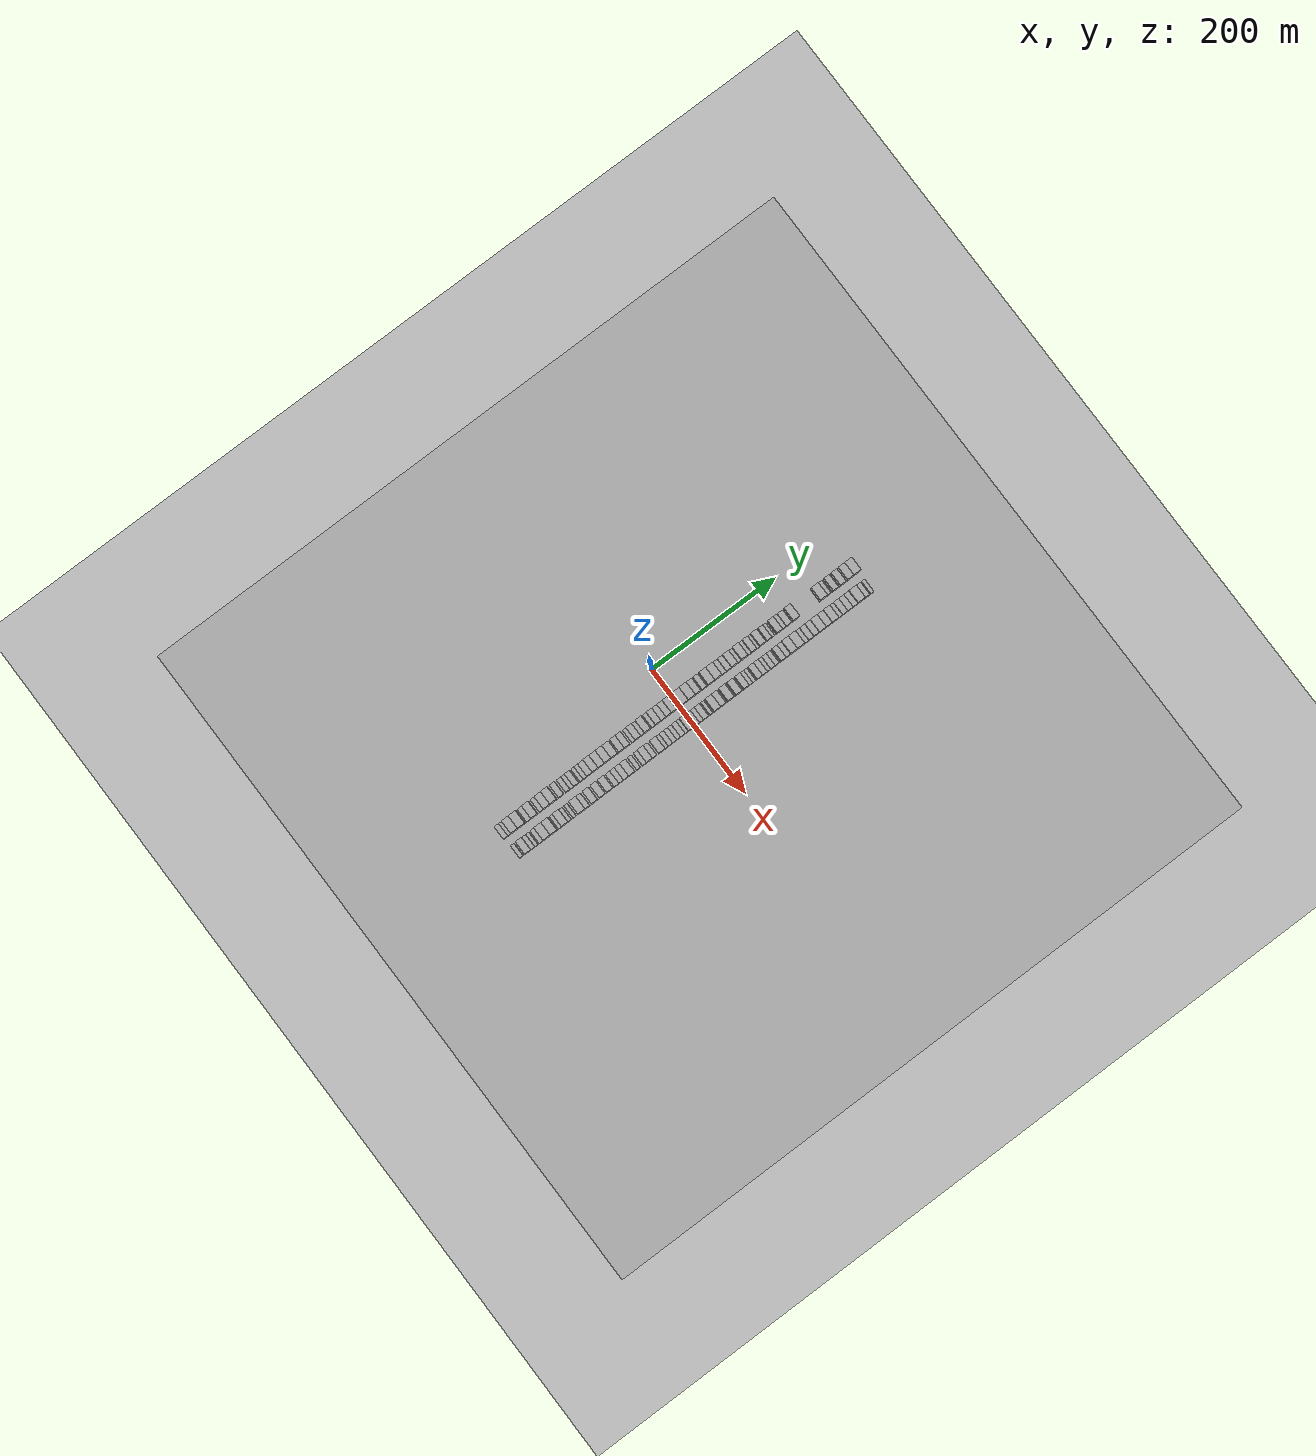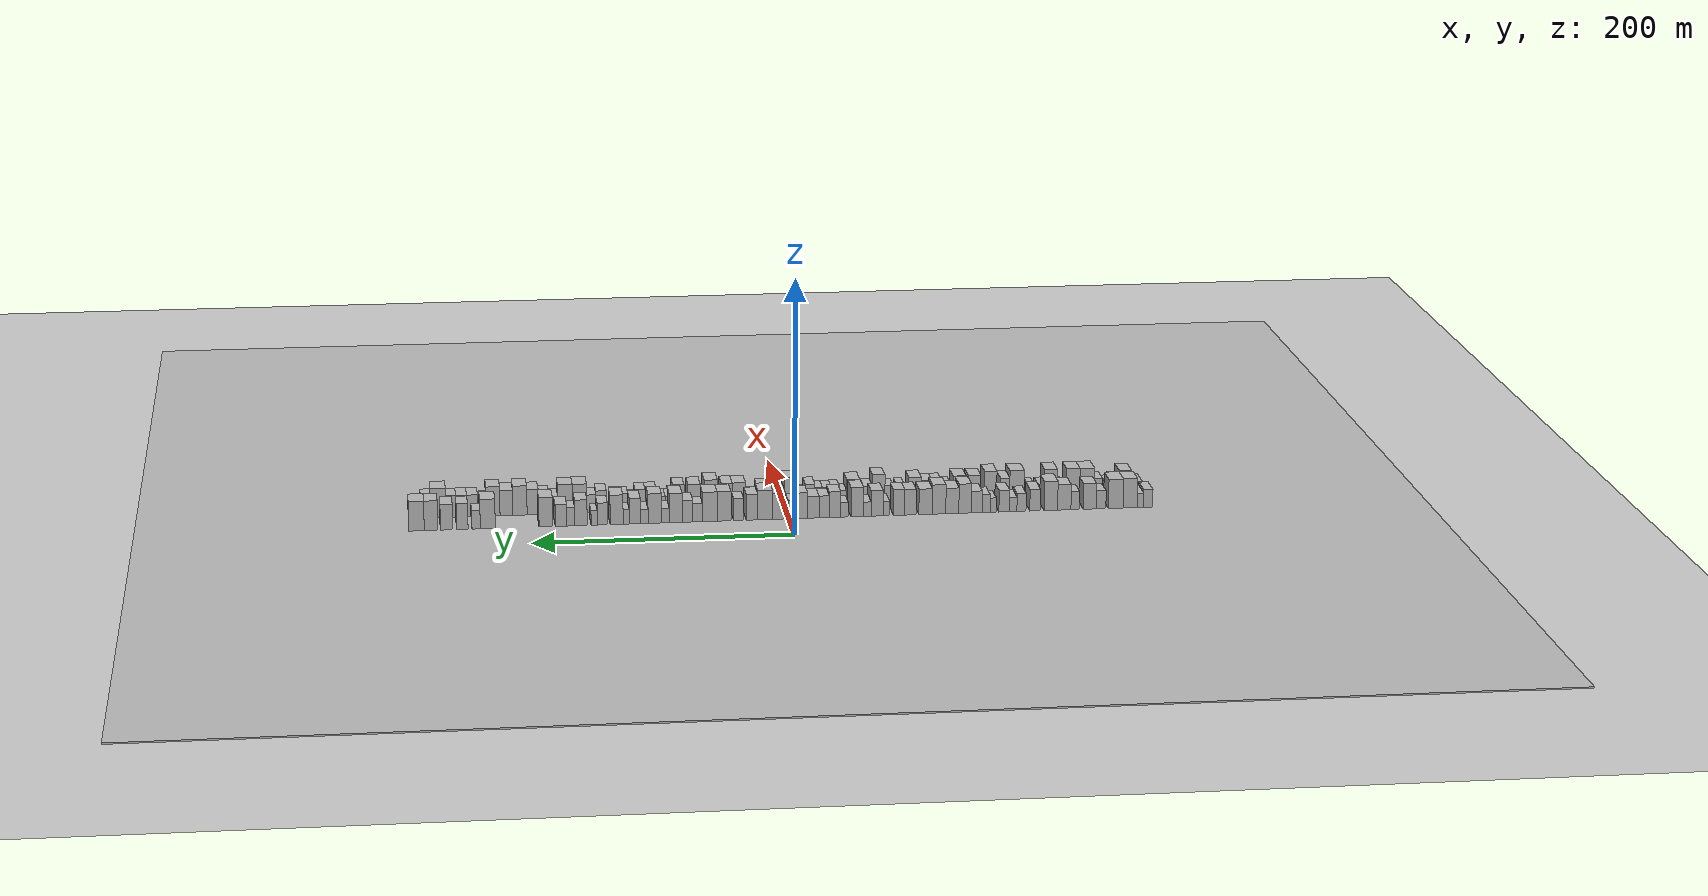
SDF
<?xml version="1.0" encoding="utf-8"?>

<sdf version="1.6">

   <world name="default">

      <gui fullscreen="0">

         <camera name="user_camera">

            <pose>-15 0 4.57585 0 0 0</pose>

            <view_controller>orbit</view_controller>

         </camera>

      </gui>

      <scene>

         <sky>

           <clouds>

             <speed>12</speed>

           </clouds>

         </sky>

         <ambient>0.4 0.4 0.4 1</ambient>

         <background>0.7 0.7 0.7 1</background>

         <shadows>1</shadows>

      </scene>

      <gravity>0 0 -9.8066</gravity>

      <magnetic_field>6e-06 2.3e-05 -4.2e-05</magnetic_field>

      <physics default="0" name="default_physics" type="ode">

         <ode>

            <solver>

               <type>quick</type>

               <iters>10</iters>

               <sor>1.0</sor>

               <use_dynamic_moi_rescaling>0</use_dynamic_moi_rescaling>

            </solver>

            <constraints>

               <cfm>0</cfm>

               <erp>0.2</erp>

               <contact_max_correcting_vel>100</contact_max_correcting_vel>

               <contact_surface_layer>0.001</contact_surface_layer>

            </constraints>

         </ode>

         <max_step_size>0.004</max_step_size>

         <real_time_factor>1</real_time_factor>

         <real_time_update_rate>250</real_time_update_rate>

      </physics>

      <light name="sun" type="directional">

         <cast_shadows>1</cast_shadows>

         <pose>0 0 10 0 0 0</pose>

         <diffuse>0.8 0.8 0.8 1</diffuse>

         <specular>0.2 0.2 0.2 1</specular>

         <attenuation>

            <range>1000</range>

            <constant>0.9</constant>

            <linear>0.01</linear>

            <quadratic>0.001</quadratic>

         </attenuation>

         <direction>-0.5 0.1 -0.9</direction>

      </light>

      <include>

         <name>ground_plane_1</name>

         <uri>model://HANNAS_ground_plane</uri>

         <pose>0 0 0  0 0 0</pose>

      </include>

      <include>

         <name>ground_plane_2</name>

         <uri>model://HANNAS_ground_plane</uri>

         <pose>100 0 0  0 0 0</pose>

      </include>

      <model name="building_1">

         <static>1</static>

         <pose frame="">50.0000 -280.4300 0 0.000000 0.000000 0.000000</pose>

         <link name="link">

            <pose frame="">0 0 7.50 0 0 0</pose>

            <collision name="collision">

               <geometry>

                  <box>

                     <size>20.0000 7.1401 15.0000</size>

                  </box>

               </geometry>

               <max_contacts>10</max_contacts>

               <surface>

                  <contact>

                     <ode/>

                  </contact>

                  <bounce/>

                  <friction>

                     <torsional>

                        <ode/>

                     </torsional>

                     <ode/>

                  </friction>

               </surface>

            </collision>

            <visual name="visual">

               <cast_shadows>0</cast_shadows>

               <geometry>

                  <box>

                     <size>20.0000 7.1401 15.0000</size>

                  </box>

               </geometry>

               <material>

                  <script>

                     <uri>model://HANNAS_wall/materials/scripts</uri>

                     <uri>model://HANNAS_wall/materials/textures</uri>

                     <name>vrc/HANNAS_wall</name>

                  </script>

               </material>

            </visual>

            <self_collide>0</self_collide>

            <enable_wind>0</enable_wind>

            <kinematic>0</kinematic>

         </link>

      </model>

      <model name="building_2">

         <static>1</static>

         <pose frame="">50.0000 -274.3220 0 0.000000 0.000000 0.000000</pose>

         <link name="link">

            <pose frame="">0 0 6.00 0 0 0</pose>

            <collision name="collision">

               <geometry>

                  <box>

                     <size>20.0000 5.0758 12.0000</size>

                  </box>

               </geometry>

               <max_contacts>10</max_contacts>

               <surface>

                  <contact>

                     <ode/>

                  </contact>

                  <bounce/>

                  <friction>

                     <torsional>

                        <ode/>

                     </torsional>

                     <ode/>

                  </friction>

               </surface>

            </collision>

            <visual name="visual">

               <cast_shadows>0</cast_shadows>

               <geometry>

                  <box>

                     <size>20.0000 5.0758 12.0000</size>

                  </box>

               </geometry>

               <material>

                  <script>

                     <uri>model://HANNAS_wall/materials/scripts</uri>

                     <uri>model://HANNAS_wall/materials/textures</uri>

                     <name>vrc/HANNAS_wall</name>

                  </script>

               </material>

            </visual>

            <self_collide>0</self_collide>

            <enable_wind>0</enable_wind>

            <kinematic>0</kinematic>

         </link>

      </model>

      <model name="building_3">

         <static>1</static>

         <pose frame="">50.0000 -266.2725 0 0.000000 0.000000 0.000000</pose>

         <link name="link">

            <pose frame="">0 0 12.00 0 0 0</pose>

            <collision name="collision">

               <geometry>

                  <box>

                     <size>20.0000 11.0232 24.0000</size>

                  </box>

               </geometry>

               <max_contacts>10</max_contacts>

               <surface>

                  <contact>

                     <ode/>

                  </contact>

                  <bounce/>

                  <friction>

                     <torsional>

                        <ode/>

                     </torsional>

                     <ode/>

                  </friction>

               </surface>

            </collision>

            <visual name="visual">

               <cast_shadows>0</cast_shadows>

               <geometry>

                  <box>

                     <size>20.0000 11.0232 24.0000</size>

                  </box>

               </geometry>

               <material>

                  <script>

                     <uri>model://HANNAS_wall/materials/scripts</uri>

                     <uri>model://HANNAS_wall/materials/textures</uri>

                     <name>vrc/HANNAS_wall</name>

                  </script>

               </material>

            </visual>

            <self_collide>0</self_collide>

            <enable_wind>0</enable_wind>

            <kinematic>0</kinematic>

         </link>

      </model>

      <model name="building_4">

         <static>1</static>

         <pose frame="">50.0000 -254.9526 0 0.000000 0.000000 0.000000</pose>

         <link name="link">

            <pose frame="">0 0 12.00 0 0 0</pose>

            <collision name="collision">

               <geometry>

                  <box>

                     <size>20.0000 11.6165 24.0000</size>

                  </box>

               </geometry>

               <max_contacts>10</max_contacts>

               <surface>

                  <contact>

                     <ode/>

                  </contact>

                  <bounce/>

                  <friction>

                     <torsional>

                        <ode/>

                     </torsional>

                     <ode/>

                  </friction>

               </surface>

            </collision>

            <visual name="visual">

               <cast_shadows>0</cast_shadows>

               <geometry>

                  <box>

                     <size>20.0000 11.6165 24.0000</size>

                  </box>

               </geometry>

               <material>

                  <script>

                     <uri>model://HANNAS_wall/materials/scripts</uri>

                     <uri>model://HANNAS_wall/materials/textures</uri>

                     <name>vrc/HANNAS_wall</name>

                  </script>

               </material>

            </visual>

            <self_collide>0</self_collide>

            <enable_wind>0</enable_wind>

            <kinematic>0</kinematic>

         </link>

      </model>

      <model name="building_5">

         <static>1</static>

         <pose frame="">50.0000 -243.4171 0 0.000000 0.000000 0.000000</pose>

         <link name="link">

            <pose frame="">0 0 7.50 0 0 0</pose>

            <collision name="collision">

               <geometry>

                  <box>

                     <size>20.0000 7.4547 15.0000</size>

                  </box>

               </geometry>

               <max_contacts>10</max_contacts>

               <surface>

                  <contact>

                     <ode/>

                  </contact>

                  <bounce/>

                  <friction>

                     <torsional>

                        <ode/>

                     </torsional>

                     <ode/>

                  </friction>

               </surface>

            </collision>

            <visual name="visual">

               <cast_shadows>0</cast_shadows>

               <geometry>

                  <box>

                     <size>20.0000 7.4547 15.0000</size>

                  </box>

               </geometry>

               <material>

                  <script>

                     <uri>model://HANNAS_wall/materials/scripts</uri>

                     <uri>model://HANNAS_wall/materials/textures</uri>

                     <name>vrc/HANNAS_wall</name>

                  </script>

               </material>

            </visual>

            <self_collide>0</self_collide>

            <enable_wind>0</enable_wind>

            <kinematic>0</kinematic>

         </link>

      </model>

      <model name="building_6">

         <static>1</static>

         <pose frame="">50.0000 -234.5609 0 0.000000 0.000000 0.000000</pose>

         <link name="link">

            <pose frame="">0 0 10.50 0 0 0</pose>

            <collision name="collision">

               <geometry>

                  <box>

                     <size>20.0000 10.2577 21.0000</size>

                  </box>

               </geometry>

               <max_contacts>10</max_contacts>

               <surface>

                  <contact>

                     <ode/>

                  </contact>

                  <bounce/>

                  <friction>

                     <torsional>

                        <ode/>

                     </torsional>

                     <ode/>

                  </friction>

               </surface>

            </collision>

            <visual name="visual">

               <cast_shadows>0</cast_shadows>

               <geometry>

                  <box>

                     <size>20.0000 10.2577 21.0000</size>

                  </box>

               </geometry>

               <material>

                  <script>

                     <uri>model://HANNAS_wall/materials/scripts</uri>

                     <uri>model://HANNAS_wall/materials/textures</uri>

                     <name>vrc/HANNAS_wall</name>

                  </script>

               </material>

            </visual>

            <self_collide>0</self_collide>

            <enable_wind>0</enable_wind>

            <kinematic>0</kinematic>

         </link>

      </model>

      <model name="building_7">

         <static>1</static>

         <pose frame="">50.0000 -223.0473 0 0.000000 0.000000 0.000000</pose>

         <link name="link">

            <pose frame="">0 0 7.50 0 0 0</pose>

            <collision name="collision">

               <geometry>

                  <box>

                     <size>20.0000 6.7694 15.0000</size>

                  </box>

               </geometry>

               <max_contacts>10</max_contacts>

               <surface>

                  <contact>

                     <ode/>

                  </contact>

                  <bounce/>

                  <friction>

                     <torsional>

                        <ode/>

                     </torsional>

                     <ode/>

                  </friction>

               </surface>

            </collision>

            <visual name="visual">

               <cast_shadows>0</cast_shadows>

               <geometry>

                  <box>

                     <size>20.0000 6.7694 15.0000</size>

                  </box>

               </geometry>

               <material>

                  <script>

                     <uri>model://HANNAS_wall/materials/scripts</uri>

                     <uri>model://HANNAS_wall/materials/textures</uri>

                     <name>vrc/HANNAS_wall</name>

                  </script>

               </material>

            </visual>

            <self_collide>0</self_collide>

            <enable_wind>0</enable_wind>

            <kinematic>0</kinematic>

         </link>

      </model>

      <model name="building_8">

         <static>1</static>

         <pose frame="">50.0000 -214.4296 0 0.000000 0.000000 0.000000</pose>

         <link name="link">

            <pose frame="">0 0 10.50 0 0 0</pose>

            <collision name="collision">

               <geometry>

                  <box>

                     <size>20.0000 10.4660 21.0000</size>

                  </box>

               </geometry>

               <max_contacts>10</max_contacts>

               <surface>

                  <contact>

                     <ode/>

                  </contact>

                  <bounce/>

                  <friction>

                     <torsional>

                        <ode/>

                     </torsional>

                     <ode/>

                  </friction>

               </surface>

            </collision>

            <visual name="visual">

               <cast_shadows>0</cast_shadows>

               <geometry>

                  <box>

                     <size>20.0000 10.4660 21.0000</size>

                  </box>

               </geometry>

               <material>

                  <script>

                     <uri>model://HANNAS_wall/materials/scripts</uri>

                     <uri>model://HANNAS_wall/materials/textures</uri>

                     <name>vrc/HANNAS_wall</name>

                  </script>

               </material>

            </visual>

            <self_collide>0</self_collide>

            <enable_wind>0</enable_wind>

            <kinematic>0</kinematic>

         </link>

      </model>

      <model name="building_9">

         <static>1</static>

         <pose frame="">50.0000 -203.8691 0 0.000000 0.000000 0.000000</pose>

         <link name="link">

            <pose frame="">0 0 12.00 0 0 0</pose>

            <collision name="collision">

               <geometry>

                  <box>

                     <size>20.0000 10.6550 24.0000</size>

                  </box>

               </geometry>

               <max_contacts>10</max_contacts>

               <surface>

                  <contact>

                     <ode/>

                  </contact>

                  <bounce/>

                  <friction>

                     <torsional>

                        <ode/>

                     </torsional>

                     <ode/>

                  </friction>

               </surface>

            </collision>

            <visual name="visual">

               <cast_shadows>0</cast_shadows>

               <geometry>

                  <box>

                     <size>20.0000 10.6550 24.0000</size>

                  </box>

               </geometry>

               <material>

                  <script>

                     <uri>model://HANNAS_wall/materials/scripts</uri>

                     <uri>model://HANNAS_wall/materials/textures</uri>

                     <name>vrc/HANNAS_wall</name>

                  </script>

               </material>

            </visual>

            <self_collide>0</self_collide>

            <enable_wind>0</enable_wind>

            <kinematic>0</kinematic>

         </link>

      </model>

      <model name="building_10">

         <static>1</static>

         <pose frame="">50.0000 -191.4496 0 0.000000 0.000000 0.000000</pose>

         <link name="link">

            <pose frame="">0 0 9.00 0 0 0</pose>

            <collision name="collision">

               <geometry>

                  <box>

                     <size>20.0000 8.1842 18.0000</size>

                  </box>

               </geometry>

               <max_contacts>10</max_contacts>

               <surface>

                  <contact>

                     <ode/>

                  </contact>

                  <bounce/>

                  <friction>

                     <torsional>

                        <ode/>

                     </torsional>

                     <ode/>

                  </friction>

               </surface>

            </collision>

            <visual name="visual">

               <cast_shadows>0</cast_shadows>

               <geometry>

                  <box>

                     <size>20.0000 8.1842 18.0000</size>

                  </box>

               </geometry>

               <material>

                  <script>

                     <uri>model://HANNAS_wall/materials/scripts</uri>

                     <uri>model://HANNAS_wall/materials/textures</uri>

                     <name>vrc/HANNAS_wall</name>

                  </script>

               </material>

            </visual>

            <self_collide>0</self_collide>

            <enable_wind>0</enable_wind>

            <kinematic>0</kinematic>

         </link>

      </model>

      <model name="building_11">

         <static>1</static>

         <pose frame="">50.0000 -180.8008 0 0.000000 0.000000 0.000000</pose>

         <link name="link">

            <pose frame="">0 0 7.50 0 0 0</pose>

            <collision name="collision">

               <geometry>

                  <box>

                     <size>20.0000 7.1133 15.0000</size>

                  </box>

               </geometry>

               <max_contacts>10</max_contacts>

               <surface>

                  <contact>

                     <ode/>

                  </contact>

                  <bounce/>

                  <friction>

                     <torsional>

                        <ode/>

                     </torsional>

                     <ode/>

                  </friction>

               </surface>

            </collision>

            <visual name="visual">

               <cast_shadows>0</cast_shadows>

               <geometry>

                  <box>

                     <size>20.0000 7.1133 15.0000</size>

                  </box>

               </geometry>

               <material>

                  <script>

                     <uri>model://HANNAS_wall/materials/scripts</uri>

                     <uri>model://HANNAS_wall/materials/textures</uri>

                     <name>vrc/HANNAS_wall</name>

                  </script>

               </material>

            </visual>

            <self_collide>0</self_collide>

            <enable_wind>0</enable_wind>

            <kinematic>0</kinematic>

         </link>

      </model>

      <model name="building_12">

         <static>1</static>

         <pose frame="">50.0000 -174.3327 0 0.000000 0.000000 0.000000</pose>

         <link name="link">

            <pose frame="">0 0 6.00 0 0 0</pose>

            <collision name="collision">

               <geometry>

                  <box>

                     <size>20.0000 5.8230 12.0000</size>

                  </box>

               </geometry>

               <max_contacts>10</max_contacts>

               <surface>

                  <contact>

                     <ode/>

                  </contact>

                  <bounce/>

                  <friction>

                     <torsional>

                        <ode/>

                     </torsional>

                     <ode/>

                  </friction>

               </surface>

            </collision>

            <visual name="visual">

               <cast_shadows>0</cast_shadows>

               <geometry>

                  <box>

                     <size>20.0000 5.8230 12.0000</size>

                  </box>

               </geometry>

               <material>

                  <script>

                     <uri>model://HANNAS_wall/materials/scripts</uri>

                     <uri>model://HANNAS_wall/materials/textures</uri>

                     <name>vrc/HANNAS_wall</name>

                  </script>

               </material>

            </visual>

            <self_collide>0</self_collide>

            <enable_wind>0</enable_wind>

            <kinematic>0</kinematic>

         </link>

      </model>

      <model name="building_13">

         <static>1</static>

         <pose frame="">50.0000 -167.2773 0 0.000000 0.000000 0.000000</pose>

         <link name="link">

            <pose frame="">0 0 9.00 0 0 0</pose>

            <collision name="collision">

               <geometry>

                  <box>

                     <size>20.0000 8.2878 18.0000</size>

                  </box>

               </geometry>

               <max_contacts>10</max_contacts>

               <surface>

                  <contact>

                     <ode/>

                  </contact>

                  <bounce/>

                  <friction>

                     <torsional>

                        <ode/>

                     </torsional>

                     <ode/>

                  </friction>

               </surface>

            </collision>

            <visual name="visual">

               <cast_shadows>0</cast_shadows>

               <geometry>

                  <box>

                     <size>20.0000 8.2878 18.0000</size>

                  </box>

               </geometry>

               <material>

                  <script>

                     <uri>model://HANNAS_wall/materials/scripts</uri>

                     <uri>model://HANNAS_wall/materials/textures</uri>

                     <name>vrc/HANNAS_wall</name>

                  </script>

               </material>

            </visual>

            <self_collide>0</self_collide>

            <enable_wind>0</enable_wind>

            <kinematic>0</kinematic>

         </link>

      </model>

      <model name="building_14">

         <static>1</static>

         <pose frame="">50.0000 -158.6507 0 0.000000 0.000000 0.000000</pose>

         <link name="link">

            <pose frame="">0 0 6.00 0 0 0</pose>

            <collision name="collision">

               <geometry>

                  <box>

                     <size>20.0000 4.9654 12.0000</size>

                  </box>

               </geometry>

               <max_contacts>10</max_contacts>

               <surface>

                  <contact>

                     <ode/>

                  </contact>

                  <bounce/>

                  <friction>

                     <torsional>

                        <ode/>

                     </torsional>

                     <ode/>

                  </friction>

               </surface>

            </collision>

            <visual name="visual">

               <cast_shadows>0</cast_shadows>

               <geometry>

                  <box>

                     <size>20.0000 4.9654 12.0000</size>

                  </box>

               </geometry>

               <material>

                  <script>

                     <uri>model://HANNAS_wall/materials/scripts</uri>

                     <uri>model://HANNAS_wall/materials/textures</uri>

                     <name>vrc/HANNAS_wall</name>

                  </script>

               </material>

            </visual>

            <self_collide>0</self_collide>

            <enable_wind>0</enable_wind>

            <kinematic>0</kinematic>

         </link>

      </model>

      <model name="building_15">

         <static>1</static>

         <pose frame="">50.0000 -153.1409 0 0.000000 0.000000 0.000000</pose>

         <link name="link">

            <pose frame="">0 0 7.50 0 0 0</pose>

            <collision name="collision">

               <geometry>

                  <box>

                     <size>20.0000 6.0542 15.0000</size>

                  </box>

               </geometry>

               <max_contacts>10</max_contacts>

               <surface>

                  <contact>

                     <ode/>

                  </contact>

                  <bounce/>

                  <friction>

                     <torsional>

                        <ode/>

                     </torsional>

                     <ode/>

                  </friction>

               </surface>

            </collision>

            <visual name="visual">

               <cast_shadows>0</cast_shadows>

               <geometry>

                  <box>

                     <size>20.0000 6.0542 15.0000</size>

                  </box>

               </geometry>

               <material>

                  <script>

                     <uri>model://HANNAS_wall/materials/scripts</uri>

                     <uri>model://HANNAS_wall/materials/textures</uri>

                     <name>vrc/HANNAS_wall</name>

                  </script>

               </material>

            </visual>

            <self_collide>0</self_collide>

            <enable_wind>0</enable_wind>

            <kinematic>0</kinematic>

         </link>

      </model>

      <model name="building_16">

         <static>1</static>

         <pose frame="">50.0000 -145.7998 0 0.000000 0.000000 0.000000</pose>

         <link name="link">

            <pose frame="">0 0 9.00 0 0 0</pose>

            <collision name="collision">

               <geometry>

                  <box>

                     <size>20.0000 8.6280 18.0000</size>

                  </box>

               </geometry>

               <max_contacts>10</max_contacts>

               <surface>

                  <contact>

                     <ode/>

                  </contact>

                  <bounce/>

                  <friction>

                     <torsional>

                        <ode/>

                     </torsional>

                     <ode/>

                  </friction>

               </surface>

            </collision>

            <visual name="visual">

               <cast_shadows>0</cast_shadows>

               <geometry>

                  <box>

                     <size>20.0000 8.6280 18.0000</size>

                  </box>

               </geometry>

               <material>

                  <script>

                     <uri>model://HANNAS_wall/materials/scripts</uri>

                     <uri>model://HANNAS_wall/materials/textures</uri>

                     <name>vrc/HANNAS_wall</name>

                  </script>

               </material>

            </visual>

            <self_collide>0</self_collide>

            <enable_wind>0</enable_wind>

            <kinematic>0</kinematic>

         </link>

      </model>

      <model name="building_17">

         <static>1</static>

         <pose frame="">50.0000 -136.6325 0 0.000000 0.000000 0.000000</pose>

         <link name="link">

            <pose frame="">0 0 12.00 0 0 0</pose>

            <collision name="collision">

               <geometry>

                  <box>

                     <size>20.0000 9.7068 24.0000</size>

                  </box>

               </geometry>

               <max_contacts>10</max_contacts>

               <surface>

                  <contact>

                     <ode/>

                  </contact>

                  <bounce/>

                  <friction>

                     <torsional>

                        <ode/>

                     </torsional>

                     <ode/>

                  </friction>

               </surface>

            </collision>

            <visual name="visual">

               <cast_shadows>0</cast_shadows>

               <geometry>

                  <box>

                     <size>20.0000 9.7068 24.0000</size>

                  </box>

               </geometry>

               <material>

                  <script>

                     <uri>model://HANNAS_wall/materials/scripts</uri>

                     <uri>model://HANNAS_wall/materials/textures</uri>

                     <name>vrc/HANNAS_wall</name>

                  </script>

               </material>

            </visual>

            <self_collide>0</self_collide>

            <enable_wind>0</enable_wind>

            <kinematic>0</kinematic>

         </link>

      </model>

      <model name="building_18">

         <static>1</static>

         <pose frame="">50.0000 -126.6958 0 0.000000 0.000000 0.000000</pose>

         <link name="link">

            <pose frame="">0 0 10.50 0 0 0</pose>

            <collision name="collision">

               <geometry>

                  <box>

                     <size>20.0000 10.1666 21.0000</size>

                  </box>

               </geometry>

               <max_contacts>10</max_contacts>

               <surface>

                  <contact>

                     <ode/>

                  </contact>

                  <bounce/>

                  <friction>

                     <torsional>

                        <ode/>

                     </torsional>

                     <ode/>

                  </friction>

               </surface>

            </collision>

            <visual name="visual">

               <cast_shadows>0</cast_shadows>

               <geometry>

                  <box>

                     <size>20.0000 10.1666 21.0000</size>

                  </box>

               </geometry>

               <material>

                  <script>

                     <uri>model://HANNAS_wall/materials/scripts</uri>

                     <uri>model://HANNAS_wall/materials/textures</uri>

                     <name>vrc/HANNAS_wall</name>

                  </script>

               </material>

            </visual>

            <self_collide>0</self_collide>

            <enable_wind>0</enable_wind>

            <kinematic>0</kinematic>

         </link>

      </model>

      <model name="building_19">

         <static>1</static>

         <pose frame="">50.0000 -116.3341 0 0.000000 0.000000 0.000000</pose>

         <link name="link">

            <pose frame="">0 0 12.00 0 0 0</pose>

            <collision name="collision">

               <geometry>

                  <box>

                     <size>20.0000 10.5568 24.0000</size>

                  </box>

               </geometry>

               <max_contacts>10</max_contacts>

               <surface>

                  <contact>

                     <ode/>

                  </contact>

                  <bounce/>

                  <friction>

                     <torsional>

                        <ode/>

                     </torsional>

                     <ode/>

                  </friction>

               </surface>

            </collision>

            <visual name="visual">

               <cast_shadows>0</cast_shadows>

               <geometry>

                  <box>

                     <size>20.0000 10.5568 24.0000</size>

                  </box>

               </geometry>

               <material>

                  <script>

                     <uri>model://HANNAS_wall/materials/scripts</uri>

                     <uri>model://HANNAS_wall/materials/textures</uri>

                     <name>vrc/HANNAS_wall</name>

                  </script>

               </material>

            </visual>

            <self_collide>0</self_collide>

            <enable_wind>0</enable_wind>

            <kinematic>0</kinematic>

         </link>

      </model>

      <model name="building_20">

         <static>1</static>

         <pose frame="">50.0000 -105.8217 0 0.000000 0.000000 0.000000</pose>

         <link name="link">

            <pose frame="">0 0 10.50 0 0 0</pose>

            <collision name="collision">

               <geometry>

                  <box>

                     <size>20.0000 10.4680 21.0000</size>

                  </box>

               </geometry>

               <max_contacts>10</max_contacts>

               <surface>

                  <contact>

                     <ode/>

                  </contact>

                  <bounce/>

                  <friction>

                     <torsional>

                        <ode/>

                     </torsional>

                     <ode/>

                  </friction>

               </surface>

            </collision>

            <visual name="visual">

               <cast_shadows>0</cast_shadows>

               <geometry>

                  <box>

                     <size>20.0000 10.4680 21.0000</size>

                  </box>

               </geometry>

               <material>

                  <script>

                     <uri>model://HANNAS_wall/materials/scripts</uri>

                     <uri>model://HANNAS_wall/materials/textures</uri>

                     <name>vrc/HANNAS_wall</name>

                  </script>

               </material>

            </visual>

            <self_collide>0</self_collide>

            <enable_wind>0</enable_wind>

            <kinematic>0</kinematic>

         </link>

      </model>

      <model name="building_21">

         <static>1</static>

         <pose frame="">50.0000 -94.0558 0 0.000000 0.000000 0.000000</pose>

         <link name="link">

            <pose frame="">0 0 10.50 0 0 0</pose>

            <collision name="collision">

               <geometry>

                  <box>

                     <size>20.0000 9.0638 21.0000</size>

                  </box>

               </geometry>

               <max_contacts>10</max_contacts>

               <surface>

                  <contact>

                     <ode/>

                  </contact>

                  <bounce/>

                  <friction>

                     <torsional>

                        <ode/>

                     </torsional>

                     <ode/>

                  </friction>

               </surface>

            </collision>

            <visual name="visual">

               <cast_shadows>0</cast_shadows>

               <geometry>

                  <box>

                     <size>20.0000 9.0638 21.0000</size>

                  </box>

               </geometry>

               <material>

                  <script>

                     <uri>model://HANNAS_wall/materials/scripts</uri>

                     <uri>model://HANNAS_wall/materials/textures</uri>

                     <name>vrc/HANNAS_wall</name>

                  </script>

               </material>

            </visual>

            <self_collide>0</self_collide>

            <enable_wind>0</enable_wind>

            <kinematic>0</kinematic>

         </link>

      </model>

      <model name="building_22">

         <static>1</static>

         <pose frame="">50.0000 -85.1823 0 0.000000 0.000000 0.000000</pose>

         <link name="link">

            <pose frame="">0 0 10.50 0 0 0</pose>

            <collision name="collision">

               <geometry>

                  <box>

                     <size>20.0000 8.6832 21.0000</size>

                  </box>

               </geometry>

               <max_contacts>10</max_contacts>

               <surface>

                  <contact>

                     <ode/>

                  </contact>

                  <bounce/>

                  <friction>

                     <torsional>

                        <ode/>

                     </torsional>

                     <ode/>

                  </friction>

               </surface>

            </collision>

            <visual name="visual">

               <cast_shadows>0</cast_shadows>

               <geometry>

                  <box>

                     <size>20.0000 8.6832 21.0000</size>

                  </box>

               </geometry>

               <material>

                  <script>

                     <uri>model://HANNAS_wall/materials/scripts</uri>

                     <uri>model://HANNAS_wall/materials/textures</uri>

                     <name>vrc/HANNAS_wall</name>

                  </script>

               </material>

            </visual>

            <self_collide>0</self_collide>

            <enable_wind>0</enable_wind>

            <kinematic>0</kinematic>

         </link>

      </model>

      <model name="building_23">

         <static>1</static>

         <pose frame="">50.0000 -75.2520 0 0.000000 0.000000 0.000000</pose>

         <link name="link">

            <pose frame="">0 0 6.00 0 0 0</pose>

            <collision name="collision">

               <geometry>

                  <box>

                     <size>20.0000 5.1775 12.0000</size>

                  </box>

               </geometry>

               <max_contacts>10</max_contacts>

               <surface>

                  <contact>

                     <ode/>

                  </contact>

                  <bounce/>

                  <friction>

                     <torsional>

                        <ode/>

                     </torsional>

                     <ode/>

                  </friction>

               </surface>

            </collision>

            <visual name="visual">

               <cast_shadows>0</cast_shadows>

               <geometry>

                  <box>

                     <size>20.0000 5.1775 12.0000</size>

                  </box>

               </geometry>

               <material>

                  <script>

                     <uri>model://HANNAS_wall/materials/scripts</uri>

                     <uri>model://HANNAS_wall/materials/textures</uri>

                     <name>vrc/HANNAS_wall</name>

                  </script>

               </material>

            </visual>

            <self_collide>0</self_collide>

            <enable_wind>0</enable_wind>

            <kinematic>0</kinematic>

         </link>

      </model>

      <model name="building_24">

         <static>1</static>

         <pose frame="">50.0000 -68.0340 0 0.000000 0.000000 0.000000</pose>

         <link name="link">

            <pose frame="">0 0 10.50 0 0 0</pose>

            <collision name="collision">

               <geometry>

                  <box>

                     <size>20.0000 9.2584 21.0000</size>

                  </box>

               </geometry>

               <max_contacts>10</max_contacts>

               <surface>

                  <contact>

                     <ode/>

                  </contact>

                  <bounce/>

                  <friction>

                     <torsional>

                        <ode/>

                     </torsional>

                     <ode/>

                  </friction>

               </surface>

            </collision>

            <visual name="visual">

               <cast_shadows>0</cast_shadows>

               <geometry>

                  <box>

                     <size>20.0000 9.2584 21.0000</size>

                  </box>

               </geometry>

               <material>

                  <script>

                     <uri>model://HANNAS_wall/materials/scripts</uri>

                     <uri>model://HANNAS_wall/materials/textures</uri>

                     <name>vrc/HANNAS_wall</name>

                  </script>

               </material>

            </visual>

            <self_collide>0</self_collide>

            <enable_wind>0</enable_wind>

            <kinematic>0</kinematic>

         </link>

      </model>

      <model name="building_25">

         <static>1</static>

         <pose frame="">50.0000 -60.4463 0 0.000000 0.000000 0.000000</pose>

         <link name="link">

            <pose frame="">0 0 6.00 0 0 0</pose>

            <collision name="collision">

               <geometry>

                  <box>

                     <size>20.0000 5.9170 12.0000</size>

                  </box>

               </geometry>

               <max_contacts>10</max_contacts>

               <surface>

                  <contact>

                     <ode/>

                  </contact>

                  <bounce/>

                  <friction>

                     <torsional>

                        <ode/>

                     </torsional>

                     <ode/>

                  </friction>

               </surface>

            </collision>

            <visual name="visual">

               <cast_shadows>0</cast_shadows>

               <geometry>

                  <box>

                     <size>20.0000 5.9170 12.0000</size>

                  </box>

               </geometry>

               <material>

                  <script>

                     <uri>model://HANNAS_wall/materials/scripts</uri>

                     <uri>model://HANNAS_wall/materials/textures</uri>

                     <name>vrc/HANNAS_wall</name>

                  </script>

               </material>

            </visual>

            <self_collide>0</self_collide>

            <enable_wind>0</enable_wind>

            <kinematic>0</kinematic>

         </link>

      </model>

      <model name="building_26">

         <static>1</static>

         <pose frame="">50.0000 -52.6109 0 0.000000 0.000000 0.000000</pose>

         <link name="link">

            <pose frame="">0 0 12.00 0 0 0</pose>

            <collision name="collision">

               <geometry>

                  <box>

                     <size>20.0000 9.7540 24.0000</size>

                  </box>

               </geometry>

               <max_contacts>10</max_contacts>

               <surface>

                  <contact>

                     <ode/>

                  </contact>

                  <bounce/>

                  <friction>

                     <torsional>

                        <ode/>

                     </torsional>

                     <ode/>

                  </friction>

               </surface>

            </collision>

            <visual name="visual">

               <cast_shadows>0</cast_shadows>

               <geometry>

                  <box>

                     <size>20.0000 9.7540 24.0000</size>

                  </box>

               </geometry>

               <material>

                  <script>

                     <uri>model://HANNAS_wall/materials/scripts</uri>

                     <uri>model://HANNAS_wall/materials/textures</uri>

                     <name>vrc/HANNAS_wall</name>

                  </script>

               </material>

            </visual>

            <self_collide>0</self_collide>

            <enable_wind>0</enable_wind>

            <kinematic>0</kinematic>

         </link>

      </model>

      <model name="building_27">

         <static>1</static>

         <pose frame="">50.0000 -42.7771 0 0.000000 0.000000 0.000000</pose>

         <link name="link">

            <pose frame="">0 0 6.00 0 0 0</pose>

            <collision name="collision">

               <geometry>

                  <box>

                     <size>20.0000 5.9135 12.0000</size>

                  </box>

               </geometry>

               <max_contacts>10</max_contacts>

               <surface>

                  <contact>

                     <ode/>

                  </contact>

                  <bounce/>

                  <friction>

                     <torsional>

                        <ode/>

                     </torsional>

                     <ode/>

                  </friction>

               </surface>

            </collision>

            <visual name="visual">

               <cast_shadows>0</cast_shadows>

               <geometry>

                  <box>

                     <size>20.0000 5.9135 12.0000</size>

                  </box>

               </geometry>

               <material>

                  <script>

                     <uri>model://HANNAS_wall/materials/scripts</uri>

                     <uri>model://HANNAS_wall/materials/textures</uri>

                     <name>vrc/HANNAS_wall</name>

                  </script>

               </material>

            </visual>

            <self_collide>0</self_collide>

            <enable_wind>0</enable_wind>

            <kinematic>0</kinematic>

         </link>

      </model>

      <model name="building_28">

         <static>1</static>

         <pose frame="">50.0000 -35.3607 0 0.000000 0.000000 0.000000</pose>

         <link name="link">

            <pose frame="">0 0 10.50 0 0 0</pose>

            <collision name="collision">

               <geometry>

                  <box>

                     <size>20.0000 8.9193 21.0000</size>

                  </box>

               </geometry>

               <max_contacts>10</max_contacts>

               <surface>

                  <contact>

                     <ode/>

                  </contact>

                  <bounce/>

                  <friction>

                     <torsional>

                        <ode/>

                     </torsional>

                     <ode/>

                  </friction>

               </surface>

            </collision>

            <visual name="visual">

               <cast_shadows>0</cast_shadows>

               <geometry>

                  <box>

                     <size>20.0000 8.9193 21.0000</size>

                  </box>

               </geometry>

               <material>

                  <script>

                     <uri>model://HANNAS_wall/materials/scripts</uri>

                     <uri>model://HANNAS_wall/materials/textures</uri>

                     <name>vrc/HANNAS_wall</name>

                  </script>

               </material>

            </visual>

            <self_collide>0</self_collide>

            <enable_wind>0</enable_wind>

            <kinematic>0</kinematic>

         </link>

      </model>

      <model name="building_29">

         <static>1</static>

         <pose frame="">50.0000 -26.9006 0 0.000000 0.000000 0.000000</pose>

         <link name="link">

            <pose frame="">0 0 9.00 0 0 0</pose>

            <collision name="collision">

               <geometry>

                  <box>

                     <size>20.0000 8.0008 18.0000</size>

                  </box>

               </geometry>

               <max_contacts>10</max_contacts>

               <surface>

                  <contact>

                     <ode/>

                  </contact>

                  <bounce/>

                  <friction>

                     <torsional>

                        <ode/>

                     </torsional>

                     <ode/>

                  </friction>

               </surface>

            </collision>

            <visual name="visual">

               <cast_shadows>0</cast_shadows>

               <geometry>

                  <box>

                     <size>20.0000 8.0008 18.0000</size>

                  </box>

               </geometry>

               <material>

                  <script>

                     <uri>model://HANNAS_wall/materials/scripts</uri>

                     <uri>model://HANNAS_wall/materials/textures</uri>

                     <name>vrc/HANNAS_wall</name>

                  </script>

               </material>

            </visual>

            <self_collide>0</self_collide>

            <enable_wind>0</enable_wind>

            <kinematic>0</kinematic>

         </link>

      </model>

      <model name="building_30">

         <static>1</static>

         <pose frame="">50.0000 -18.5486 0 0.000000 0.000000 0.000000</pose>

         <link name="link">

            <pose frame="">0 0 9.00 0 0 0</pose>

            <collision name="collision">

               <geometry>

                  <box>

                     <size>20.0000 8.7033 18.0000</size>

                  </box>

               </geometry>

               <max_contacts>10</max_contacts>

               <surface>

                  <contact>

                     <ode/>

                  </contact>

                  <bounce/>

                  <friction>

                     <torsional>

                        <ode/>

                     </torsional>

                     <ode/>

                  </friction>

               </surface>

            </collision>

            <visual name="visual">

               <cast_shadows>0</cast_shadows>

               <geometry>

                  <box>

                     <size>20.0000 8.7033 18.0000</size>

                  </box>

               </geometry>

               <material>

                  <script>

                     <uri>model://HANNAS_wall/materials/scripts</uri>

                     <uri>model://HANNAS_wall/materials/textures</uri>

                     <name>vrc/HANNAS_wall</name>

                  </script>

               </material>

            </visual>

            <self_collide>0</self_collide>

            <enable_wind>0</enable_wind>

            <kinematic>0</kinematic>

         </link>

      </model>

      <model name="building_31">

         <static>1</static>

         <pose frame="">50.0000 -9.9834 0 0.000000 0.000000 0.000000</pose>

         <link name="link">

            <pose frame="">0 0 10.50 0 0 0</pose>

            <collision name="collision">

               <geometry>

                  <box>

                     <size>20.0000 8.4271 21.0000</size>

                  </box>

               </geometry>

               <max_contacts>10</max_contacts>

               <surface>

                  <contact>

                     <ode/>

                  </contact>

                  <bounce/>

                  <friction>

                     <torsional>

                        <ode/>

                     </torsional>

                     <ode/>

                  </friction>

               </surface>

            </collision>

            <visual name="visual">

               <cast_shadows>0</cast_shadows>

               <geometry>

                  <box>

                     <size>20.0000 8.4271 21.0000</size>

                  </box>

               </geometry>

               <material>

                  <script>

                     <uri>model://HANNAS_wall/materials/scripts</uri>

                     <uri>model://HANNAS_wall/materials/textures</uri>

                     <name>vrc/HANNAS_wall</name>

                  </script>

               </material>

            </visual>

            <self_collide>0</self_collide>

            <enable_wind>0</enable_wind>

            <kinematic>0</kinematic>

         </link>

      </model>

      <model name="building_32">

         <static>1</static>

         <pose frame="">50.0000 -2.4643 0 0.000000 0.000000 0.000000</pose>

         <link name="link">

            <pose frame="">0 0 7.50 0 0 0</pose>

            <collision name="collision">

               <geometry>

                  <box>

                     <size>20.0000 6.6110 15.0000</size>

                  </box>

               </geometry>

               <max_contacts>10</max_contacts>

               <surface>

                  <contact>

                     <ode/>

                  </contact>

                  <bounce/>

                  <friction>

                     <torsional>

                        <ode/>

                     </torsional>

                     <ode/>

                  </friction>

               </surface>

            </collision>

            <visual name="visual">

               <cast_shadows>0</cast_shadows>

               <geometry>

                  <box>

                     <size>20.0000 6.6110 15.0000</size>

                  </box>

               </geometry>

               <material>

                  <script>

                     <uri>model://HANNAS_wall/materials/scripts</uri>

                     <uri>model://HANNAS_wall/materials/textures</uri>

                     <name>vrc/HANNAS_wall</name>

                  </script>

               </material>

            </visual>

            <self_collide>0</self_collide>

            <enable_wind>0</enable_wind>

            <kinematic>0</kinematic>

         </link>

      </model>

      <model name="building_33">

         <static>1</static>

         <pose frame="">50.0000 7.9757 0 0.000000 0.000000 0.000000</pose>

         <link name="link">

            <pose frame="">0 0 10.50 0 0 0</pose>

            <collision name="collision">

               <geometry>

                  <box>

                     <size>20.0000 10.2690 21.0000</size>

                  </box>

               </geometry>

               <max_contacts>10</max_contacts>

               <surface>

                  <contact>

                     <ode/>

                  </contact>

                  <bounce/>

                  <friction>

                     <torsional>

                        <ode/>

                     </torsional>

                     <ode/>

                  </friction>

               </surface>

            </collision>

            <visual name="visual">

               <cast_shadows>0</cast_shadows>

               <geometry>

                  <box>

                     <size>20.0000 10.2690 21.0000</size>

                  </box>

               </geometry>

               <material>

                  <script>

                     <uri>model://HANNAS_wall/materials/scripts</uri>

                     <uri>model://HANNAS_wall/materials/textures</uri>

                     <name>vrc/HANNAS_wall</name>

                  </script>

               </material>

            </visual>

            <self_collide>0</self_collide>

            <enable_wind>0</enable_wind>

            <kinematic>0</kinematic>

         </link>

      </model>

      <model name="building_34">

         <static>1</static>

         <pose frame="">50.0000 18.7712 0 0.000000 0.000000 0.000000</pose>

         <link name="link">

            <pose frame="">0 0 12.00 0 0 0</pose>

            <collision name="collision">

               <geometry>

                  <box>

                     <size>20.0000 11.3220 24.0000</size>

                  </box>

               </geometry>

               <max_contacts>10</max_contacts>

               <surface>

                  <contact>

                     <ode/>

                  </contact>

                  <bounce/>

                  <friction>

                     <torsional>

                        <ode/>

                     </torsional>

                     <ode/>

                  </friction>

               </surface>

            </collision>

            <visual name="visual">

               <cast_shadows>0</cast_shadows>

               <geometry>

                  <box>

                     <size>20.0000 11.3220 24.0000</size>

                  </box>

               </geometry>

               <material>

                  <script>

                     <uri>model://HANNAS_wall/materials/scripts</uri>

                     <uri>model://HANNAS_wall/materials/textures</uri>

                     <name>vrc/HANNAS_wall</name>

                  </script>

               </material>

            </visual>

            <self_collide>0</self_collide>

            <enable_wind>0</enable_wind>

            <kinematic>0</kinematic>

         </link>

      </model>

      <model name="building_35">

         <static>1</static>

         <pose frame="">50.0000 28.8956 0 0.000000 0.000000 0.000000</pose>

         <link name="link">

            <pose frame="">0 0 10.50 0 0 0</pose>

            <collision name="collision">

               <geometry>

                  <box>

                     <size>20.0000 8.9268 21.0000</size>

                  </box>

               </geometry>

               <max_contacts>10</max_contacts>

               <surface>

                  <contact>

                     <ode/>

                  </contact>

                  <bounce/>

                  <friction>

                     <torsional>

                        <ode/>

                     </torsional>

                     <ode/>

                  </friction>

               </surface>

            </collision>

            <visual name="visual">

               <cast_shadows>0</cast_shadows>

               <geometry>

                  <box>

                     <size>20.0000 8.9268 21.0000</size>

                  </box>

               </geometry>

               <material>

                  <script>

                     <uri>model://HANNAS_wall/materials/scripts</uri>

                     <uri>model://HANNAS_wall/materials/textures</uri>

                     <name>vrc/HANNAS_wall</name>

                  </script>

               </material>

            </visual>

            <self_collide>0</self_collide>

            <enable_wind>0</enable_wind>

            <kinematic>0</kinematic>

         </link>

      </model>

      <model name="building_36">

         <static>1</static>

         <pose frame="">50.0000 39.2411 0 0.000000 0.000000 0.000000</pose>

         <link name="link">

            <pose frame="">0 0 9.00 0 0 0</pose>

            <collision name="collision">

               <geometry>

                  <box>

                     <size>20.0000 7.7642 18.0000</size>

                  </box>

               </geometry>

               <max_contacts>10</max_contacts>

               <surface>

                  <contact>

                     <ode/>

                  </contact>

                  <bounce/>

                  <friction>

                     <torsional>

                        <ode/>

                     </torsional>

                     <ode/>

                  </friction>

               </surface>

            </collision>

            <visual name="visual">

               <cast_shadows>0</cast_shadows>

               <geometry>

                  <box>

                     <size>20.0000 7.7642 18.0000</size>

                  </box>

               </geometry>

               <material>

                  <script>

                     <uri>model://HANNAS_wall/materials/scripts</uri>

                     <uri>model://HANNAS_wall/materials/textures</uri>

                     <name>vrc/HANNAS_wall</name>

                  </script>

               </material>

            </visual>

            <self_collide>0</self_collide>

            <enable_wind>0</enable_wind>

            <kinematic>0</kinematic>

         </link>

      </model>

      <model name="building_37">

         <static>1</static>

         <pose frame="">50.0000 50.4694 0 0.000000 0.000000 0.000000</pose>

         <link name="link">

            <pose frame="">0 0 12.00 0 0 0</pose>

            <collision name="collision">

               <geometry>

                  <box>

                     <size>20.0000 10.6924 24.0000</size>

                  </box>

               </geometry>

               <max_contacts>10</max_contacts>

               <surface>

                  <contact>

                     <ode/>

                  </contact>

                  <bounce/>

                  <friction>

                     <torsional>

                        <ode/>

                     </torsional>

                     <ode/>

                  </friction>

               </surface>

            </collision>

            <visual name="visual">

               <cast_shadows>0</cast_shadows>

               <geometry>

                  <box>

                     <size>20.0000 10.6924 24.0000</size>

                  </box>

               </geometry>

               <material>

                  <script>

                     <uri>model://HANNAS_wall/materials/scripts</uri>

                     <uri>model://HANNAS_wall/materials/textures</uri>

                     <name>vrc/HANNAS_wall</name>

                  </script>

               </material>

            </visual>

            <self_collide>0</self_collide>

            <enable_wind>0</enable_wind>

            <kinematic>0</kinematic>

         </link>

      </model>

      <model name="building_38">

         <static>1</static>

         <pose frame="">50.0000 61.5156 0 0.000000 0.000000 0.000000</pose>

         <link name="link">

            <pose frame="">0 0 12.00 0 0 0</pose>

            <collision name="collision">

               <geometry>

                  <box>

                     <size>20.0000 11.3999 24.0000</size>

                  </box>

               </geometry>

               <max_contacts>10</max_contacts>

               <surface>

                  <contact>

                     <ode/>

                  </contact>

                  <bounce/>

                  <friction>

                     <torsional>

                        <ode/>

                     </torsional>

                     <ode/>

                  </friction>

               </surface>

            </collision>

            <visual name="visual">

               <cast_shadows>0</cast_shadows>

               <geometry>

                  <box>

                     <size>20.0000 11.3999 24.0000</size>

                  </box>

               </geometry>

               <material>

                  <script>

                     <uri>model://HANNAS_wall/materials/scripts</uri>

                     <uri>model://HANNAS_wall/materials/textures</uri>

                     <name>vrc/HANNAS_wall</name>

                  </script>

               </material>

            </visual>

            <self_collide>0</self_collide>

            <enable_wind>0</enable_wind>

            <kinematic>0</kinematic>

         </link>

      </model>

      <model name="building_39">

         <static>1</static>

         <pose frame="">50.0000 70.9410 0 0.000000 0.000000 0.000000</pose>

         <link name="link">

            <pose frame="">0 0 7.50 0 0 0</pose>

            <collision name="collision">

               <geometry>

                  <box>

                     <size>20.0000 7.4509 15.0000</size>

                  </box>

               </geometry>

               <max_contacts>10</max_contacts>

               <surface>

                  <contact>

                     <ode/>

                  </contact>

                  <bounce/>

                  <friction>

                     <torsional>

                        <ode/>

                     </torsional>

                     <ode/>

                  </friction>

               </surface>

            </collision>

            <visual name="visual">

               <cast_shadows>0</cast_shadows>

               <geometry>

                  <box>

                     <size>20.0000 7.4509 15.0000</size>

                  </box>

               </geometry>

               <material>

                  <script>

                     <uri>model://HANNAS_wall/materials/scripts</uri>

                     <uri>model://HANNAS_wall/materials/textures</uri>

                     <name>vrc/HANNAS_wall</name>

                  </script>

               </material>

            </visual>

            <self_collide>0</self_collide>

            <enable_wind>0</enable_wind>

            <kinematic>0</kinematic>

         </link>

      </model>

      <model name="building_40">

         <static>1</static>

         <pose frame="">50.0000 78.7618 0 0.000000 0.000000 0.000000</pose>

         <link name="link">

            <pose frame="">0 0 9.00 0 0 0</pose>

            <collision name="collision">

               <geometry>

                  <box>

                     <size>20.0000 8.1908 18.0000</size>

                  </box>

               </geometry>

               <max_contacts>10</max_contacts>

               <surface>

                  <contact>

                     <ode/>

                  </contact>

                  <bounce/>

                  <friction>

                     <torsional>

                        <ode/>

                     </torsional>

                     <ode/>

                  </friction>

               </surface>

            </collision>

            <visual name="visual">

               <cast_shadows>0</cast_shadows>

               <geometry>

                  <box>

                     <size>20.0000 8.1908 18.0000</size>

                  </box>

               </geometry>

               <material>

                  <script>

                     <uri>model://HANNAS_wall/materials/scripts</uri>

                     <uri>model://HANNAS_wall/materials/textures</uri>

                     <name>vrc/HANNAS_wall</name>

                  </script>

               </material>

            </visual>

            <self_collide>0</self_collide>

            <enable_wind>0</enable_wind>

            <kinematic>0</kinematic>

         </link>

      </model>

      <model name="building_41">

         <static>1</static>

         <pose frame="">50.0000 87.8269 0 0.000000 0.000000 0.000000</pose>

         <link name="link">

            <pose frame="">0 0 12.00 0 0 0</pose>

            <collision name="collision">

               <geometry>

                  <box>

                     <size>20.0000 9.9394 24.0000</size>

                  </box>

               </geometry>

               <max_contacts>10</max_contacts>

               <surface>

                  <contact>

                     <ode/>

                  </contact>

                  <bounce/>

                  <friction>

                     <torsional>

                        <ode/>

                     </torsional>

                     <ode/>

                  </friction>

               </surface>

            </collision>

            <visual name="visual">

               <cast_shadows>0</cast_shadows>

               <geometry>

                  <box>

                     <size>20.0000 9.9394 24.0000</size>

                  </box>

               </geometry>

               <material>

                  <script>

                     <uri>model://HANNAS_wall/materials/scripts</uri>

                     <uri>model://HANNAS_wall/materials/textures</uri>

                     <name>vrc/HANNAS_wall</name>

                  </script>

               </material>

            </visual>

            <self_collide>0</self_collide>

            <enable_wind>0</enable_wind>

            <kinematic>0</kinematic>

         </link>

      </model>

      <model name="building_42">

         <static>1</static>

         <pose frame="">50.0000 95.7598 0 0.000000 0.000000 0.000000</pose>

         <link name="link">

            <pose frame="">0 0 6.00 0 0 0</pose>

            <collision name="collision">

               <geometry>

                  <box>

                     <size>20.0000 5.9263 12.0000</size>

                  </box>

               </geometry>

               <max_contacts>10</max_contacts>

               <surface>

                  <contact>

                     <ode/>

                  </contact>

                  <bounce/>

                  <friction>

                     <torsional>

                        <ode/>

                     </torsional>

                     <ode/>

                  </friction>

               </surface>

            </collision>

            <visual name="visual">

               <cast_shadows>0</cast_shadows>

               <geometry>

                  <box>

                     <size>20.0000 5.9263 12.0000</size>

                  </box>

               </geometry>

               <material>

                  <script>

                     <uri>model://HANNAS_wall/materials/scripts</uri>

                     <uri>model://HANNAS_wall/materials/textures</uri>

                     <name>vrc/HANNAS_wall</name>

                  </script>

               </material>

            </visual>

            <self_collide>0</self_collide>

            <enable_wind>0</enable_wind>

            <kinematic>0</kinematic>

         </link>

      </model>

      <model name="building_43">

         <static>1</static>

         <pose frame="">50.0000 103.9115 0 0.000000 0.000000 0.000000</pose>

         <link name="link">

            <pose frame="">0 0 12.00 0 0 0</pose>

            <collision name="collision">

               <geometry>

                  <box>

                     <size>20.0000 10.3771 24.0000</size>

                  </box>

               </geometry>

               <max_contacts>10</max_contacts>

               <surface>

                  <contact>

                     <ode/>

                  </contact>

                  <bounce/>

                  <friction>

                     <torsional>

                        <ode/>

                     </torsional>

                     <ode/>

                  </friction>

               </surface>

            </collision>

            <visual name="visual">

               <cast_shadows>0</cast_shadows>

               <geometry>

                  <box>

                     <size>20.0000 10.3771 24.0000</size>

                  </box>

               </geometry>

               <material>

                  <script>

                     <uri>model://HANNAS_wall/materials/scripts</uri>

                     <uri>model://HANNAS_wall/materials/textures</uri>

                     <name>vrc/HANNAS_wall</name>

                  </script>

               </material>

            </visual>

            <self_collide>0</self_collide>

            <enable_wind>0</enable_wind>

            <kinematic>0</kinematic>

         </link>

      </model>

      <model name="building_44">

         <static>1</static>

         <pose frame="">50.0000 112.0410 0 0.000000 0.000000 0.000000</pose>

         <link name="link">

            <pose frame="">0 0 6.00 0 0 0</pose>

            <collision name="collision">

               <geometry>

                  <box>

                     <size>20.0000 5.8819 12.0000</size>

                  </box>

               </geometry>

               <max_contacts>10</max_contacts>

               <surface>

                  <contact>

                     <ode/>

                  </contact>

                  <bounce/>

                  <friction>

                     <torsional>

                        <ode/>

                     </torsional>

                     <ode/>

                  </friction>

               </surface>

            </collision>

            <visual name="visual">

               <cast_shadows>0</cast_shadows>

               <geometry>

                  <box>

                     <size>20.0000 5.8819 12.0000</size>

                  </box>

               </geometry>

               <material>

                  <script>

                     <uri>model://HANNAS_wall/materials/scripts</uri>

                     <uri>model://HANNAS_wall/materials/textures</uri>

                     <name>vrc/HANNAS_wall</name>

                  </script>

               </material>

            </visual>

            <self_collide>0</self_collide>

            <enable_wind>0</enable_wind>

            <kinematic>0</kinematic>

         </link>

      </model>

      <model name="building_45">

         <static>1</static>

         <pose frame="">50.0000 119.2341 0 0.000000 0.000000 0.000000</pose>

         <link name="link">

            <pose frame="">0 0 10.50 0 0 0</pose>

            <collision name="collision">

               <geometry>

                  <box>

                     <size>20.0000 8.5043 21.0000</size>

                  </box>

               </geometry>

               <max_contacts>10</max_contacts>

               <surface>

                  <contact>

                     <ode/>

                  </contact>

                  <bounce/>

                  <friction>

                     <torsional>

                        <ode/>

                     </torsional>

                     <ode/>

                  </friction>

               </surface>

            </collision>

            <visual name="visual">

               <cast_shadows>0</cast_shadows>

               <geometry>

                  <box>

                     <size>20.0000 8.5043 21.0000</size>

                  </box>

               </geometry>

               <material>

                  <script>

                     <uri>model://HANNAS_wall/materials/scripts</uri>

                     <uri>model://HANNAS_wall/materials/textures</uri>

                     <name>vrc/HANNAS_wall</name>

                  </script>

               </material>

            </visual>

            <self_collide>0</self_collide>

            <enable_wind>0</enable_wind>

            <kinematic>0</kinematic>

         </link>

      </model>

      <model name="building_46">

         <static>1</static>

         <pose frame="">50.0000 125.8914 0 0.000000 0.000000 0.000000</pose>

         <link name="link">

            <pose frame="">0 0 6.00 0 0 0</pose>

            <collision name="collision">

               <geometry>

                  <box>

                     <size>20.0000 4.8104 12.0000</size>

                  </box>

               </geometry>

               <max_contacts>10</max_contacts>

               <surface>

                  <contact>

                     <ode/>

                  </contact>

                  <bounce/>

                  <friction>

                     <torsional>

                        <ode/>

                     </torsional>

                     <ode/>

                  </friction>

               </surface>

            </collision>

            <visual name="visual">

               <cast_shadows>0</cast_shadows>

               <geometry>

                  <box>

                     <size>20.0000 4.8104 12.0000</size>

                  </box>

               </geometry>

               <material>

                  <script>

                     <uri>model://HANNAS_wall/materials/scripts</uri>

                     <uri>model://HANNAS_wall/materials/textures</uri>

                     <name>vrc/HANNAS_wall</name>

                  </script>

               </material>

            </visual>

            <self_collide>0</self_collide>

            <enable_wind>0</enable_wind>

            <kinematic>0</kinematic>

         </link>

      </model>

      <model name="building_47">

         <static>1</static>

         <pose frame="">50.0000 133.2575 0 0.000000 0.000000 0.000000</pose>

         <link name="link">

            <pose frame="">0 0 12.00 0 0 0</pose>

            <collision name="collision">

               <geometry>

                  <box>

                     <size>20.0000 9.9218 24.0000</size>

                  </box>

               </geometry>

               <max_contacts>10</max_contacts>

               <surface>

                  <contact>

                     <ode/>

                  </contact>

                  <bounce/>

                  <friction>

                     <torsional>

                        <ode/>

                     </torsional>

                     <ode/>

                  </friction>

               </surface>

            </collision>

            <visual name="visual">

               <cast_shadows>0</cast_shadows>

               <geometry>

                  <box>

                     <size>20.0000 9.9218 24.0000</size>

                  </box>

               </geometry>

               <material>

                  <script>

                     <uri>model://HANNAS_wall/materials/scripts</uri>

                     <uri>model://HANNAS_wall/materials/textures</uri>

                     <name>vrc/HANNAS_wall</name>

                  </script>

               </material>

            </visual>

            <self_collide>0</self_collide>

            <enable_wind>0</enable_wind>

            <kinematic>0</kinematic>

         </link>

      </model>

      <model name="building_48">

         <static>1</static>

         <pose frame="">50.0000 144.1445 0 0.000000 0.000000 0.000000</pose>

         <link name="link">

            <pose frame="">0 0 9.00 0 0 0</pose>

            <collision name="collision">

               <geometry>

                  <box>

                     <size>20.0000 7.8521 18.0000</size>

                  </box>

               </geometry>

               <max_contacts>10</max_contacts>

               <surface>

                  <contact>

                     <ode/>

                  </contact>

                  <bounce/>

                  <friction>

                     <torsional>

                        <ode/>

                     </torsional>

                     <ode/>

                  </friction>

               </surface>

            </collision>

            <visual name="visual">

               <cast_shadows>0</cast_shadows>

               <geometry>

                  <box>

                     <size>20.0000 7.8521 18.0000</size>

                  </box>

               </geometry>

               <material>

                  <script>

                     <uri>model://HANNAS_wall/materials/scripts</uri>

                     <uri>model://HANNAS_wall/materials/textures</uri>

                     <name>vrc/HANNAS_wall</name>

                  </script>

               </material>

            </visual>

            <self_collide>0</self_collide>

            <enable_wind>0</enable_wind>

            <kinematic>0</kinematic>

         </link>

      </model>

      <model name="building_49">

         <static>1</static>

         <pose frame="">50.0000 150.4758 0 0.000000 0.000000 0.000000</pose>

         <link name="link">

            <pose frame="">0 0 6.00 0 0 0</pose>

            <collision name="collision">

               <geometry>

                  <box>

                     <size>20.0000 4.8105 12.0000</size>

                  </box>

               </geometry>

               <max_contacts>10</max_contacts>

               <surface>

                  <contact>

                     <ode/>

                  </contact>

                  <bounce/>

                  <friction>

                     <torsional>

                        <ode/>

                     </torsional>

                     <ode/>

                  </friction>

               </surface>

            </collision>

            <visual name="visual">

               <cast_shadows>0</cast_shadows>

               <geometry>

                  <box>

                     <size>20.0000 4.8105 12.0000</size>

                  </box>

               </geometry>

               <material>

                  <script>

                     <uri>model://HANNAS_wall/materials/scripts</uri>

                     <uri>model://HANNAS_wall/materials/textures</uri>

                     <name>vrc/HANNAS_wall</name>

                  </script>

               </material>

            </visual>

            <self_collide>0</self_collide>

            <enable_wind>0</enable_wind>

            <kinematic>0</kinematic>

         </link>

      </model>

      <model name="building_50">

         <static>1</static>

         <pose frame="">50.0000 160.5811 0 0.000000 0.000000 0.000000</pose>

         <link name="link">

            <pose frame="">0 0 10.50 0 0 0</pose>

            <collision name="collision">

               <geometry>

                  <box>

                     <size>20.0000 9.4002 21.0000</size>

                  </box>

               </geometry>

               <max_contacts>10</max_contacts>

               <surface>

                  <contact>

                     <ode/>

                  </contact>

                  <bounce/>

                  <friction>

                     <torsional>

                        <ode/>

                     </torsional>

                     <ode/>

                  </friction>

               </surface>

            </collision>

            <visual name="visual">

               <cast_shadows>0</cast_shadows>

               <geometry>

                  <box>

                     <size>20.0000 9.4002 21.0000</size>

                  </box>

               </geometry>

               <material>

                  <script>

                     <uri>model://HANNAS_wall/materials/scripts</uri>

                     <uri>model://HANNAS_wall/materials/textures</uri>

                     <name>vrc/HANNAS_wall</name>

                  </script>

               </material>

            </visual>

            <self_collide>0</self_collide>

            <enable_wind>0</enable_wind>

            <kinematic>0</kinematic>

         </link>

      </model>

      <model name="building_51">

         <static>1</static>

         <pose frame="">50.0000 168.3770 0 0.000000 0.000000 0.000000</pose>

         <link name="link">

            <pose frame="">0 0 7.50 0 0 0</pose>

            <collision name="collision">

               <geometry>

                  <box>

                     <size>20.0000 6.1916 15.0000</size>

                  </box>

               </geometry>

               <max_contacts>10</max_contacts>

               <surface>

                  <contact>

                     <ode/>

                  </contact>

                  <bounce/>

                  <friction>

                     <torsional>

                        <ode/>

                     </torsional>

                     <ode/>

                  </friction>

               </surface>

            </collision>

            <visual name="visual">

               <cast_shadows>0</cast_shadows>

               <geometry>

                  <box>

                     <size>20.0000 6.1916 15.0000</size>

                  </box>

               </geometry>

               <material>

                  <script>

                     <uri>model://HANNAS_wall/materials/scripts</uri>

                     <uri>model://HANNAS_wall/materials/textures</uri>

                     <name>vrc/HANNAS_wall</name>

                  </script>

               </material>

            </visual>

            <self_collide>0</self_collide>

            <enable_wind>0</enable_wind>

            <kinematic>0</kinematic>

         </link>

      </model>

      <model name="building_52">

         <static>1</static>

         <pose frame="">50.0000 175.8885 0 0.000000 0.000000 0.000000</pose>

         <link name="link">

            <pose frame="">0 0 9.00 0 0 0</pose>

            <collision name="collision">

               <geometry>

                  <box>

                     <size>20.0000 8.8314 18.0000</size>

                  </box>

               </geometry>

               <max_contacts>10</max_contacts>

               <surface>

                  <contact>

                     <ode/>

                  </contact>

                  <bounce/>

                  <friction>

                     <torsional>

                        <ode/>

                     </torsional>

                     <ode/>

                  </friction>

               </surface>

            </collision>

            <visual name="visual">

               <cast_shadows>0</cast_shadows>

               <geometry>

                  <box>

                     <size>20.0000 8.8314 18.0000</size>

                  </box>

               </geometry>

               <material>

                  <script>

                     <uri>model://HANNAS_wall/materials/scripts</uri>

                     <uri>model://HANNAS_wall/materials/textures</uri>

                     <name>vrc/HANNAS_wall</name>

                  </script>

               </material>

            </visual>

            <self_collide>0</self_collide>

            <enable_wind>0</enable_wind>

            <kinematic>0</kinematic>

         </link>

      </model>

      <model name="building_53">

         <static>1</static>

         <pose frame="">50.0000 187.5169 0 0.000000 0.000000 0.000000</pose>

         <link name="link">

            <pose frame="">0 0 12.00 0 0 0</pose>

            <collision name="collision">

               <geometry>

                  <box>

                     <size>20.0000 10.4254 24.0000</size>

                  </box>

               </geometry>

               <max_contacts>10</max_contacts>

               <surface>

                  <contact>

                     <ode/>

                  </contact>

                  <bounce/>

                  <friction>

                     <torsional>

                        <ode/>

                     </torsional>

                     <ode/>

                  </friction>

               </surface>

            </collision>

            <visual name="visual">

               <cast_shadows>0</cast_shadows>

               <geometry>

                  <box>

                     <size>20.0000 10.4254 24.0000</size>

                  </box>

               </geometry>

               <material>

                  <script>

                     <uri>model://HANNAS_wall/materials/scripts</uri>

                     <uri>model://HANNAS_wall/materials/textures</uri>

                     <name>vrc/HANNAS_wall</name>

                  </script>

               </material>

            </visual>

            <self_collide>0</self_collide>

            <enable_wind>0</enable_wind>

            <kinematic>0</kinematic>

         </link>

      </model>

      <model name="building_54">

         <static>1</static>

         <pose frame="">50.0000 231.8937 0 0.000000 0.000000 0.000000</pose>

         <link name="link">

            <pose frame="">0 0 12.00 0 0 0</pose>

            <collision name="collision">

               <geometry>

                  <box>

                     <size>20.0000 11.4427 24.0000</size>

                  </box>

               </geometry>

               <max_contacts>10</max_contacts>

               <surface>

                  <contact>

                     <ode/>

                  </contact>

                  <bounce/>

                  <friction>

                     <torsional>

                        <ode/>

                     </torsional>

                     <ode/>

                  </friction>

               </surface>

            </collision>

            <visual name="visual">

               <cast_shadows>0</cast_shadows>

               <geometry>

                  <box>

                     <size>20.0000 11.4427 24.0000</size>

                  </box>

               </geometry>

               <material>

                  <script>

                     <uri>model://HANNAS_wall/materials/scripts</uri>

                     <uri>model://HANNAS_wall/materials/textures</uri>

                     <name>vrc/HANNAS_wall</name>

                  </script>

               </material>

            </visual>

            <self_collide>0</self_collide>

            <enable_wind>0</enable_wind>

            <kinematic>0</kinematic>

         </link>

      </model>

      <model name="building_55">

         <static>1</static>

         <pose frame="">50.0000 240.7712 0 0.000000 0.000000 0.000000</pose>

         <link name="link">

            <pose frame="">0 0 7.50 0 0 0</pose>

            <collision name="collision">

               <geometry>

                  <box>

                     <size>20.0000 6.3123 15.0000</size>

                  </box>

               </geometry>

               <max_contacts>10</max_contacts>

               <surface>

                  <contact>

                     <ode/>

                  </contact>

                  <bounce/>

                  <friction>

                     <torsional>

                        <ode/>

                     </torsional>

                     <ode/>

                  </friction>

               </surface>

            </collision>

            <visual name="visual">

               <cast_shadows>0</cast_shadows>

               <geometry>

                  <box>

                     <size>20.0000 6.3123 15.0000</size>

                  </box>

               </geometry>

               <material>

                  <script>

                     <uri>model://HANNAS_wall/materials/scripts</uri>

                     <uri>model://HANNAS_wall/materials/textures</uri>

                     <name>vrc/HANNAS_wall</name>

                  </script>

               </material>

            </visual>

            <self_collide>0</self_collide>

            <enable_wind>0</enable_wind>

            <kinematic>0</kinematic>

         </link>

      </model>

      <model name="building_56">

         <static>1</static>

         <pose frame="">50.0000 251.2696 0 0.000000 0.000000 0.000000</pose>

         <link name="link">

            <pose frame="">0 0 10.50 0 0 0</pose>

            <collision name="collision">

               <geometry>

                  <box>

                     <size>20.0000 8.6844 21.0000</size>

                  </box>

               </geometry>

               <max_contacts>10</max_contacts>

               <surface>

                  <contact>

                     <ode/>

                  </contact>

                  <bounce/>

                  <friction>

                     <torsional>

                        <ode/>

                     </torsional>

                     <ode/>

                  </friction>

               </surface>

            </collision>

            <visual name="visual">

               <cast_shadows>0</cast_shadows>

               <geometry>

                  <box>

                     <size>20.0000 8.6844 21.0000</size>

                  </box>

               </geometry>

               <material>

                  <script>

                     <uri>model://HANNAS_wall/materials/scripts</uri>

                     <uri>model://HANNAS_wall/materials/textures</uri>

                     <name>vrc/HANNAS_wall</name>

                  </script>

               </material>

            </visual>

            <self_collide>0</self_collide>

            <enable_wind>0</enable_wind>

            <kinematic>0</kinematic>

         </link>

      </model>

      <model name="building_57">

         <static>1</static>

         <pose frame="">50.0000 263.2645 0 0.000000 0.000000 0.000000</pose>

         <link name="link">

            <pose frame="">0 0 10.50 0 0 0</pose>

            <collision name="collision">

               <geometry>

                  <box>

                     <size>20.0000 9.3053 21.0000</size>

                  </box>

               </geometry>

               <max_contacts>10</max_contacts>

               <surface>

                  <contact>

                     <ode/>

                  </contact>

                  <bounce/>

                  <friction>

                     <torsional>

                        <ode/>

                     </torsional>

                     <ode/>

                  </friction>

               </surface>

            </collision>

            <visual name="visual">

               <cast_shadows>0</cast_shadows>

               <geometry>

                  <box>

                     <size>20.0000 9.3053 21.0000</size>

                  </box>

               </geometry>

               <material>

                  <script>

                     <uri>model://HANNAS_wall/materials/scripts</uri>

                     <uri>model://HANNAS_wall/materials/textures</uri>

                     <name>vrc/HANNAS_wall</name>

                  </script>

               </material>

            </visual>

            <self_collide>0</self_collide>

            <enable_wind>0</enable_wind>

            <kinematic>0</kinematic>

         </link>

      </model>

      <model name="building_58">

         <static>1</static>

         <pose frame="">50.0000 275.0928 0 0.000000 0.000000 0.000000</pose>

         <link name="link">

            <pose frame="">0 0 12.00 0 0 0</pose>

            <collision name="collision">

               <geometry>

                  <box>

                     <size>20.0000 10.3512 24.0000</size>

                  </box>

               </geometry>

               <max_contacts>10</max_contacts>

               <surface>

                  <contact>

                     <ode/>

                  </contact>

                  <bounce/>

                  <friction>

                     <torsional>

                        <ode/>

                     </torsional>

                     <ode/>

                  </friction>

               </surface>

            </collision>

            <visual name="visual">

               <cast_shadows>0</cast_shadows>

               <geometry>

                  <box>

                     <size>20.0000 10.3512 24.0000</size>

                  </box>

               </geometry>

               <material>

                  <script>

                     <uri>model://HANNAS_wall/materials/scripts</uri>

                     <uri>model://HANNAS_wall/materials/textures</uri>

                     <name>vrc/HANNAS_wall</name>

                  </script>

               </material>

            </visual>

            <self_collide>0</self_collide>

            <enable_wind>0</enable_wind>

            <kinematic>0</kinematic>

         </link>

      </model>

      <model name="building_59">

         <static>1</static>

         <pose frame="">50.0000 286.1208 0 0.000000 0.000000 0.000000</pose>

         <link name="link">

            <pose frame="">0 0 12.00 0 0 0</pose>

            <collision name="collision">

               <geometry>

                  <box>

                     <size>20.0000 11.7048 24.0000</size>

                  </box>

               </geometry>

               <max_contacts>10</max_contacts>

               <surface>

                  <contact>

                     <ode/>

                  </contact>

                  <bounce/>

                  <friction>

                     <torsional>

                        <ode/>

                     </torsional>

                     <ode/>

                  </friction>

               </surface>

            </collision>

            <visual name="visual">

               <cast_shadows>0</cast_shadows>

               <geometry>

                  <box>

                     <size>20.0000 11.7048 24.0000</size>

                  </box>

               </geometry>

               <material>

                  <script>

                     <uri>model://HANNAS_wall/materials/scripts</uri>

                     <uri>model://HANNAS_wall/materials/textures</uri>

                     <name>vrc/HANNAS_wall</name>

                  </script>

               </material>

            </visual>

            <self_collide>0</self_collide>

            <enable_wind>0</enable_wind>

            <kinematic>0</kinematic>

         </link>

      </model>

      <model name="building_60">

         <static>1</static>

         <pose frame="">82.0000 -279.2086 0 0.000000 0.000000 0.000000</pose>

         <link name="link">

            <pose frame="">0 0 6.00 0 0 0</pose>

            <collision name="collision">

               <geometry>

                  <box>

                     <size>20.0000 5.5827 12.0000</size>

                  </box>

               </geometry>

               <max_contacts>10</max_contacts>

               <surface>

                  <contact>

                     <ode/>

                  </contact>

                  <bounce/>

                  <friction>

                     <torsional>

                        <ode/>

                     </torsional>

                     <ode/>

                  </friction>

               </surface>

            </collision>

            <visual name="visual">

               <cast_shadows>0</cast_shadows>

               <geometry>

                  <box>

                     <size>20.0000 5.5827 12.0000</size>

                  </box>

               </geometry>

               <material>

                  <script>

                     <uri>model://HANNAS_wall/materials/scripts</uri>

                     <uri>model://HANNAS_wall/materials/textures</uri>

                     <name>vrc/HANNAS_wall</name>

                  </script>

               </material>

            </visual>

            <self_collide>0</self_collide>

            <enable_wind>0</enable_wind>

            <kinematic>0</kinematic>

         </link>

      </model>

      <model name="building_61">

         <static>1</static>

         <pose frame="">82.0000 -268.5561 0 0.000000 0.000000 0.000000</pose>

         <link name="link">

            <pose frame="">0 0 10.50 0 0 0</pose>

            <collision name="collision">

               <geometry>

                  <box>

                     <size>20.0000 9.7223 21.0000</size>

                  </box>

               </geometry>

               <max_contacts>10</max_contacts>

               <surface>

                  <contact>

                     <ode/>

                  </contact>

                  <bounce/>

                  <friction>

                     <torsional>

                        <ode/>

                     </torsional>

                     <ode/>

                  </friction>

               </surface>

            </collision>

            <visual name="visual">

               <cast_shadows>0</cast_shadows>

               <geometry>

                  <box>

                     <size>20.0000 9.7223 21.0000</size>

                  </box>

               </geometry>

               <material>

                  <script>

                     <uri>model://HANNAS_wall/materials/scripts</uri>

                     <uri>model://HANNAS_wall/materials/textures</uri>

                     <name>vrc/HANNAS_wall</name>

                  </script>

               </material>

            </visual>

            <self_collide>0</self_collide>

            <enable_wind>0</enable_wind>

            <kinematic>0</kinematic>

         </link>

      </model>

      <model name="building_62">

         <static>1</static>

         <pose frame="">82.0000 -260.5660 0 0.000000 0.000000 0.000000</pose>

         <link name="link">

            <pose frame="">0 0 7.50 0 0 0</pose>

            <collision name="collision">

               <geometry>

                  <box>

                     <size>20.0000 6.2579 15.0000</size>

                  </box>

               </geometry>

               <max_contacts>10</max_contacts>

               <surface>

                  <contact>

                     <ode/>

                  </contact>

                  <bounce/>

                  <friction>

                     <torsional>

                        <ode/>

                     </torsional>

                     <ode/>

                  </friction>

               </surface>

            </collision>

            <visual name="visual">

               <cast_shadows>0</cast_shadows>

               <geometry>

                  <box>

                     <size>20.0000 6.2579 15.0000</size>

                  </box>

               </geometry>

               <material>

                  <script>

                     <uri>model://HANNAS_wall/materials/scripts</uri>

                     <uri>model://HANNAS_wall/materials/textures</uri>

                     <name>vrc/HANNAS_wall</name>

                  </script>

               </material>

            </visual>

            <self_collide>0</self_collide>

            <enable_wind>0</enable_wind>

            <kinematic>0</kinematic>

         </link>

      </model>

      <model name="building_63">

         <static>1</static>

         <pose frame="">82.0000 -255.0244 0 0.000000 0.000000 0.000000</pose>

         <link name="link">

            <pose frame="">0 0 6.00 0 0 0</pose>

            <collision name="collision">

               <geometry>

                  <box>

                     <size>20.0000 4.8252 12.0000</size>

                  </box>

               </geometry>

               <max_contacts>10</max_contacts>

               <surface>

                  <contact>

                     <ode/>

                  </contact>

                  <bounce/>

                  <friction>

                     <torsional>

                        <ode/>

                     </torsional>

                     <ode/>

                  </friction>

               </surface>

            </collision>

            <visual name="visual">

               <cast_shadows>0</cast_shadows>

               <geometry>

                  <box>

                     <size>20.0000 4.8252 12.0000</size>

                  </box>

               </geometry>

               <material>

                  <script>

                     <uri>model://HANNAS_wall/materials/scripts</uri>

                     <uri>model://HANNAS_wall/materials/textures</uri>

                     <name>vrc/HANNAS_wall</name>

                  </script>

               </material>

            </visual>

            <self_collide>0</self_collide>

            <enable_wind>0</enable_wind>

            <kinematic>0</kinematic>

         </link>

      </model>

      <model name="building_64">

         <static>1</static>

         <pose frame="">82.0000 -247.2567 0 0.000000 0.000000 0.000000</pose>

         <link name="link">

            <pose frame="">0 0 7.50 0 0 0</pose>

            <collision name="collision">

               <geometry>

                  <box>

                     <size>20.0000 6.7103 15.0000</size>

                  </box>

               </geometry>

               <max_contacts>10</max_contacts>

               <surface>

                  <contact>

                     <ode/>

                  </contact>

                  <bounce/>

                  <friction>

                     <torsional>

                        <ode/>

                     </torsional>

                     <ode/>

                  </friction>

               </surface>

            </collision>

            <visual name="visual">

               <cast_shadows>0</cast_shadows>

               <geometry>

                  <box>

                     <size>20.0000 6.7103 15.0000</size>

                  </box>

               </geometry>

               <material>

                  <script>

                     <uri>model://HANNAS_wall/materials/scripts</uri>

                     <uri>model://HANNAS_wall/materials/textures</uri>

                     <name>vrc/HANNAS_wall</name>

                  </script>

               </material>

            </visual>

            <self_collide>0</self_collide>

            <enable_wind>0</enable_wind>

            <kinematic>0</kinematic>

         </link>

      </model>

      <model name="building_65">

         <static>1</static>

         <pose frame="">82.0000 -238.1398 0 0.000000 0.000000 0.000000</pose>

         <link name="link">

            <pose frame="">0 0 12.00 0 0 0</pose>

            <collision name="collision">

               <geometry>

                  <box>

                     <size>20.0000 11.5235 24.0000</size>

                  </box>

               </geometry>

               <max_contacts>10</max_contacts>

               <surface>

                  <contact>

                     <ode/>

                  </contact>

                  <bounce/>

                  <friction>

                     <torsional>

                        <ode/>

                     </torsional>

                     <ode/>

                  </friction>

               </surface>

            </collision>

            <visual name="visual">

               <cast_shadows>0</cast_shadows>

               <geometry>

                  <box>

                     <size>20.0000 11.5235 24.0000</size>

                  </box>

               </geometry>

               <material>

                  <script>

                     <uri>model://HANNAS_wall/materials/scripts</uri>

                     <uri>model://HANNAS_wall/materials/textures</uri>

                     <name>vrc/HANNAS_wall</name>

                  </script>

               </material>

            </visual>

            <self_collide>0</self_collide>

            <enable_wind>0</enable_wind>

            <kinematic>0</kinematic>

         </link>

      </model>

      <model name="building_66">

         <static>1</static>

         <pose frame="">82.0000 -227.0429 0 0.000000 0.000000 0.000000</pose>

         <link name="link">

            <pose frame="">0 0 12.00 0 0 0</pose>

            <collision name="collision">

               <geometry>

                  <box>

                     <size>20.0000 10.6705 24.0000</size>

                  </box>

               </geometry>

               <max_contacts>10</max_contacts>

               <surface>

                  <contact>

                     <ode/>

                  </contact>

                  <bounce/>

                  <friction>

                     <torsional>

                        <ode/>

                     </torsional>

                     <ode/>

                  </friction>

               </surface>

            </collision>

            <visual name="visual">

               <cast_shadows>0</cast_shadows>

               <geometry>

                  <box>

                     <size>20.0000 10.6705 24.0000</size>

                  </box>

               </geometry>

               <material>

                  <script>

                     <uri>model://HANNAS_wall/materials/scripts</uri>

                     <uri>model://HANNAS_wall/materials/textures</uri>

                     <name>vrc/HANNAS_wall</name>

                  </script>

               </material>

            </visual>

            <self_collide>0</self_collide>

            <enable_wind>0</enable_wind>

            <kinematic>0</kinematic>

         </link>

      </model>

      <model name="building_67">

         <static>1</static>

         <pose frame="">82.0000 -217.0891 0 0.000000 0.000000 0.000000</pose>

         <link name="link">

            <pose frame="">0 0 6.00 0 0 0</pose>

            <collision name="collision">

               <geometry>

                  <box>

                     <size>20.0000 5.2370 12.0000</size>

                  </box>

               </geometry>

               <max_contacts>10</max_contacts>

               <surface>

                  <contact>

                     <ode/>

                  </contact>

                  <bounce/>

                  <friction>

                     <torsional>

                        <ode/>

                     </torsional>

                     <ode/>

                  </friction>

               </surface>

            </collision>

            <visual name="visual">

               <cast_shadows>0</cast_shadows>

               <geometry>

                  <box>

                     <size>20.0000 5.2370 12.0000</size>

                  </box>

               </geometry>

               <material>

                  <script>

                     <uri>model://HANNAS_wall/materials/scripts</uri>

                     <uri>model://HANNAS_wall/materials/textures</uri>

                     <name>vrc/HANNAS_wall</name>

                  </script>

               </material>

            </visual>

            <self_collide>0</self_collide>

            <enable_wind>0</enable_wind>

            <kinematic>0</kinematic>

         </link>

      </model>

      <model name="building_68">

         <static>1</static>

         <pose frame="">82.0000 -209.4249 0 0.000000 0.000000 0.000000</pose>

         <link name="link">

            <pose frame="">0 0 12.00 0 0 0</pose>

            <collision name="collision">

               <geometry>

                  <box>

                     <size>20.0000 10.0914 24.0000</size>

                  </box>

               </geometry>

               <max_contacts>10</max_contacts>

               <surface>

                  <contact>

                     <ode/>

                  </contact>

                  <bounce/>

                  <friction>

                     <torsional>

                        <ode/>

                     </torsional>

                     <ode/>

                  </friction>

               </surface>

            </collision>

            <visual name="visual">

               <cast_shadows>0</cast_shadows>

               <geometry>

                  <box>

                     <size>20.0000 10.0914 24.0000</size>

                  </box>

               </geometry>

               <material>

                  <script>

                     <uri>model://HANNAS_wall/materials/scripts</uri>

                     <uri>model://HANNAS_wall/materials/textures</uri>

                     <name>vrc/HANNAS_wall</name>

                  </script>

               </material>

            </visual>

            <self_collide>0</self_collide>

            <enable_wind>0</enable_wind>

            <kinematic>0</kinematic>

         </link>

      </model>

      <model name="building_69">

         <static>1</static>

         <pose frame="">82.0000 -201.8696 0 0.000000 0.000000 0.000000</pose>

         <link name="link">

            <pose frame="">0 0 6.00 0 0 0</pose>

            <collision name="collision">

               <geometry>

                  <box>

                     <size>20.0000 5.0193 12.0000</size>

                  </box>

               </geometry>

               <max_contacts>10</max_contacts>

               <surface>

                  <contact>

                     <ode/>

                  </contact>

                  <bounce/>

                  <friction>

                     <torsional>

                        <ode/>

                     </torsional>

                     <ode/>

                  </friction>

               </surface>

            </collision>

            <visual name="visual">

               <cast_shadows>0</cast_shadows>

               <geometry>

                  <box>

                     <size>20.0000 5.0193 12.0000</size>

                  </box>

               </geometry>

               <material>

                  <script>

                     <uri>model://HANNAS_wall/materials/scripts</uri>

                     <uri>model://HANNAS_wall/materials/textures</uri>

                     <name>vrc/HANNAS_wall</name>

                  </script>

               </material>

            </visual>

            <self_collide>0</self_collide>

            <enable_wind>0</enable_wind>

            <kinematic>0</kinematic>

         </link>

      </model>

      <model name="building_70">

         <static>1</static>

         <pose frame="">82.0000 -193.8006 0 0.000000 0.000000 0.000000</pose>

         <link name="link">

            <pose frame="">0 0 6.00 0 0 0</pose>

            <collision name="collision">

               <geometry>

                  <box>

                     <size>20.0000 5.1186 12.0000</size>

                  </box>

               </geometry>

               <max_contacts>10</max_contacts>

               <surface>

                  <contact>

                     <ode/>

                  </contact>

                  <bounce/>

                  <friction>

                     <torsional>

                        <ode/>

                     </torsional>

                     <ode/>

                  </friction>

               </surface>

            </collision>

            <visual name="visual">

               <cast_shadows>0</cast_shadows>

               <geometry>

                  <box>

                     <size>20.0000 5.1186 12.0000</size>

                  </box>

               </geometry>

               <material>

                  <script>

                     <uri>model://HANNAS_wall/materials/scripts</uri>

                     <uri>model://HANNAS_wall/materials/textures</uri>

                     <name>vrc/HANNAS_wall</name>

                  </script>

               </material>

            </visual>

            <self_collide>0</self_collide>

            <enable_wind>0</enable_wind>

            <kinematic>0</kinematic>

         </link>

      </model>

      <model name="building_71">

         <static>1</static>

         <pose frame="">82.0000 -182.5330 0 0.000000 0.000000 0.000000</pose>

         <link name="link">

            <pose frame="">0 0 12.00 0 0 0</pose>

            <collision name="collision">

               <geometry>

                  <box>

                     <size>20.0000 11.4166 24.0000</size>

                  </box>

               </geometry>

               <max_contacts>10</max_contacts>

               <surface>

                  <contact>

                     <ode/>

                  </contact>

                  <bounce/>

                  <friction>

                     <torsional>

                        <ode/>

                     </torsional>

                     <ode/>

                  </friction>

               </surface>

            </collision>

            <visual name="visual">

               <cast_shadows>0</cast_shadows>

               <geometry>

                  <box>

                     <size>20.0000 11.4166 24.0000</size>

                  </box>

               </geometry>

               <material>

                  <script>

                     <uri>model://HANNAS_wall/materials/scripts</uri>

                     <uri>model://HANNAS_wall/materials/textures</uri>

                     <name>vrc/HANNAS_wall</name>

                  </script>

               </material>

            </visual>

            <self_collide>0</self_collide>

            <enable_wind>0</enable_wind>

            <kinematic>0</kinematic>

         </link>

      </model>

      <model name="building_72">

         <static>1</static>

         <pose frame="">82.0000 -173.1772 0 0.000000 0.000000 0.000000</pose>

         <link name="link">

            <pose frame="">0 0 9.00 0 0 0</pose>

            <collision name="collision">

               <geometry>

                  <box>

                     <size>20.0000 7.2949 18.0000</size>

                  </box>

               </geometry>

               <max_contacts>10</max_contacts>

               <surface>

                  <contact>

                     <ode/>

                  </contact>

                  <bounce/>

                  <friction>

                     <torsional>

                        <ode/>

                     </torsional>

                     <ode/>

                  </friction>

               </surface>

            </collision>

            <visual name="visual">

               <cast_shadows>0</cast_shadows>

               <geometry>

                  <box>

                     <size>20.0000 7.2949 18.0000</size>

                  </box>

               </geometry>

               <material>

                  <script>

                     <uri>model://HANNAS_wall/materials/scripts</uri>

                     <uri>model://HANNAS_wall/materials/textures</uri>

                     <name>vrc/HANNAS_wall</name>

                  </script>

               </material>

            </visual>

            <self_collide>0</self_collide>

            <enable_wind>0</enable_wind>

            <kinematic>0</kinematic>

         </link>

      </model>

      <model name="building_73">

         <static>1</static>

         <pose frame="">82.0000 -161.7076 0 0.000000 0.000000 0.000000</pose>

         <link name="link">

            <pose frame="">0 0 12.00 0 0 0</pose>

            <collision name="collision">

               <geometry>

                  <box>

                     <size>20.0000 9.6444 24.0000</size>

                  </box>

               </geometry>

               <max_contacts>10</max_contacts>

               <surface>

                  <contact>

                     <ode/>

                  </contact>

                  <bounce/>

                  <friction>

                     <torsional>

                        <ode/>

                     </torsional>

                     <ode/>

                  </friction>

               </surface>

            </collision>

            <visual name="visual">

               <cast_shadows>0</cast_shadows>

               <geometry>

                  <box>

                     <size>20.0000 9.6444 24.0000</size>

                  </box>

               </geometry>

               <material>

                  <script>

                     <uri>model://HANNAS_wall/materials/scripts</uri>

                     <uri>model://HANNAS_wall/materials/textures</uri>

                     <name>vrc/HANNAS_wall</name>

                  </script>

               </material>

            </visual>

            <self_collide>0</self_collide>

            <enable_wind>0</enable_wind>

            <kinematic>0</kinematic>

         </link>

      </model>

      <model name="building_74">

         <static>1</static>

         <pose frame="">82.0000 -149.1072 0 0.000000 0.000000 0.000000</pose>

         <link name="link">

            <pose frame="">0 0 10.50 0 0 0</pose>

            <collision name="collision">

               <geometry>

                  <box>

                     <size>20.0000 9.5562 21.0000</size>

                  </box>

               </geometry>

               <max_contacts>10</max_contacts>

               <surface>

                  <contact>

                     <ode/>

                  </contact>

                  <bounce/>

                  <friction>

                     <torsional>

                        <ode/>

                     </torsional>

                     <ode/>

                  </friction>

               </surface>

            </collision>

            <visual name="visual">

               <cast_shadows>0</cast_shadows>

               <geometry>

                  <box>

                     <size>20.0000 9.5562 21.0000</size>

                  </box>

               </geometry>

               <material>

                  <script>

                     <uri>model://HANNAS_wall/materials/scripts</uri>

                     <uri>model://HANNAS_wall/materials/textures</uri>

                     <name>vrc/HANNAS_wall</name>

                  </script>

               </material>

            </visual>

            <self_collide>0</self_collide>

            <enable_wind>0</enable_wind>

            <kinematic>0</kinematic>

         </link>

      </model>

      <model name="building_75">

         <static>1</static>

         <pose frame="">82.0000 -137.1418 0 0.000000 0.000000 0.000000</pose>

         <link name="link">

            <pose frame="">0 0 10.50 0 0 0</pose>

            <collision name="collision">

               <geometry>

                  <box>

                     <size>20.0000 10.3747 21.0000</size>

                  </box>

               </geometry>

               <max_contacts>10</max_contacts>

               <surface>

                  <contact>

                     <ode/>

                  </contact>

                  <bounce/>

                  <friction>

                     <torsional>

                        <ode/>

                     </torsional>

                     <ode/>

                  </friction>

               </surface>

            </collision>

            <visual name="visual">

               <cast_shadows>0</cast_shadows>

               <geometry>

                  <box>

                     <size>20.0000 10.3747 21.0000</size>

                  </box>

               </geometry>

               <material>

                  <script>

                     <uri>model://HANNAS_wall/materials/scripts</uri>

                     <uri>model://HANNAS_wall/materials/textures</uri>

                     <name>vrc/HANNAS_wall</name>

                  </script>

               </material>

            </visual>

            <self_collide>0</self_collide>

            <enable_wind>0</enable_wind>

            <kinematic>0</kinematic>

         </link>

      </model>

      <model name="building_76">

         <static>1</static>

         <pose frame="">82.0000 -126.2881 0 0.000000 0.000000 0.000000</pose>

         <link name="link">

            <pose frame="">0 0 7.50 0 0 0</pose>

            <collision name="collision">

               <geometry>

                  <box>

                     <size>20.0000 7.3325 15.0000</size>

                  </box>

               </geometry>

               <max_contacts>10</max_contacts>

               <surface>

                  <contact>

                     <ode/>

                  </contact>

                  <bounce/>

                  <friction>

                     <torsional>

                        <ode/>

                     </torsional>

                     <ode/>

                  </friction>

               </surface>

            </collision>

            <visual name="visual">

               <cast_shadows>0</cast_shadows>

               <geometry>

                  <box>

                     <size>20.0000 7.3325 15.0000</size>

                  </box>

               </geometry>

               <material>

                  <script>

                     <uri>model://HANNAS_wall/materials/scripts</uri>

                     <uri>model://HANNAS_wall/materials/textures</uri>

                     <name>vrc/HANNAS_wall</name>

                  </script>

               </material>

            </visual>

            <self_collide>0</self_collide>

            <enable_wind>0</enable_wind>

            <kinematic>0</kinematic>

         </link>

      </model>

      <model name="building_77">

         <static>1</static>

         <pose frame="">82.0000 -119.0209 0 0.000000 0.000000 0.000000</pose>

         <link name="link">

            <pose frame="">0 0 9.00 0 0 0</pose>

            <collision name="collision">

               <geometry>

                  <box>

                     <size>20.0000 7.2019 18.0000</size>

                  </box>

               </geometry>

               <max_contacts>10</max_contacts>

               <surface>

                  <contact>

                     <ode/>

                  </contact>

                  <bounce/>

                  <friction>

                     <torsional>

                        <ode/>

                     </torsional>

                     <ode/>

                  </friction>

               </surface>

            </collision>

            <visual name="visual">

               <cast_shadows>0</cast_shadows>

               <geometry>

                  <box>

                     <size>20.0000 7.2019 18.0000</size>

                  </box>

               </geometry>

               <material>

                  <script>

                     <uri>model://HANNAS_wall/materials/scripts</uri>

                     <uri>model://HANNAS_wall/materials/textures</uri>

                     <name>vrc/HANNAS_wall</name>

                  </script>

               </material>

            </visual>

            <self_collide>0</self_collide>

            <enable_wind>0</enable_wind>

            <kinematic>0</kinematic>

         </link>

      </model>

      <model name="building_78">

         <static>1</static>

         <pose frame="">82.0000 -111.1388 0 0.000000 0.000000 0.000000</pose>

         <link name="link">

            <pose frame="">0 0 9.00 0 0 0</pose>

            <collision name="collision">

               <geometry>

                  <box>

                     <size>20.0000 8.5622 18.0000</size>

                  </box>

               </geometry>

               <max_contacts>10</max_contacts>

               <surface>

                  <contact>

                     <ode/>

                  </contact>

                  <bounce/>

                  <friction>

                     <torsional>

                        <ode/>

                     </torsional>

                     <ode/>

                  </friction>

               </surface>

            </collision>

            <visual name="visual">

               <cast_shadows>0</cast_shadows>

               <geometry>

                  <box>

                     <size>20.0000 8.5622 18.0000</size>

                  </box>

               </geometry>

               <material>

                  <script>

                     <uri>model://HANNAS_wall/materials/scripts</uri>

                     <uri>model://HANNAS_wall/materials/textures</uri>

                     <name>vrc/HANNAS_wall</name>

                  </script>

               </material>

            </visual>

            <self_collide>0</self_collide>

            <enable_wind>0</enable_wind>

            <kinematic>0</kinematic>

         </link>

      </model>

      <model name="building_79">

         <static>1</static>

         <pose frame="">82.0000 -101.9360 0 0.000000 0.000000 0.000000</pose>

         <link name="link">

            <pose frame="">0 0 10.50 0 0 0</pose>

            <collision name="collision">

               <geometry>

                  <box>

                     <size>20.0000 9.8434 21.0000</size>

                  </box>

               </geometry>

               <max_contacts>10</max_contacts>

               <surface>

                  <contact>

                     <ode/>

                  </contact>

                  <bounce/>

                  <friction>

                     <torsional>

                        <ode/>

                     </torsional>

                     <ode/>

                  </friction>

               </surface>

            </collision>

            <visual name="visual">

               <cast_shadows>0</cast_shadows>

               <geometry>

                  <box>

                     <size>20.0000 9.8434 21.0000</size>

                  </box>

               </geometry>

               <material>

                  <script>

                     <uri>model://HANNAS_wall/materials/scripts</uri>

                     <uri>model://HANNAS_wall/materials/textures</uri>

                     <name>vrc/HANNAS_wall</name>

                  </script>

               </material>

            </visual>

            <self_collide>0</self_collide>

            <enable_wind>0</enable_wind>

            <kinematic>0</kinematic>

         </link>

      </model>

      <model name="building_80">

         <static>1</static>

         <pose frame="">82.0000 -90.8969 0 0.000000 0.000000 0.000000</pose>

         <link name="link">

            <pose frame="">0 0 7.50 0 0 0</pose>

            <collision name="collision">

               <geometry>

                  <box>

                     <size>20.0000 6.2347 15.0000</size>

                  </box>

               </geometry>

               <max_contacts>10</max_contacts>

               <surface>

                  <contact>

                     <ode/>

                  </contact>

                  <bounce/>

                  <friction>

                     <torsional>

                        <ode/>

                     </torsional>

                     <ode/>

                  </friction>

               </surface>

            </collision>

            <visual name="visual">

               <cast_shadows>0</cast_shadows>

               <geometry>

                  <box>

                     <size>20.0000 6.2347 15.0000</size>

                  </box>

               </geometry>

               <material>

                  <script>

                     <uri>model://HANNAS_wall/materials/scripts</uri>

                     <uri>model://HANNAS_wall/materials/textures</uri>

                     <name>vrc/HANNAS_wall</name>

                  </script>

               </material>

            </visual>

            <self_collide>0</self_collide>

            <enable_wind>0</enable_wind>

            <kinematic>0</kinematic>

         </link>

      </model>

      <model name="building_81">

         <static>1</static>

         <pose frame="">82.0000 -81.5745 0 0.000000 0.000000 0.000000</pose>

         <link name="link">

            <pose frame="">0 0 7.50 0 0 0</pose>

            <collision name="collision">

               <geometry>

                  <box>

                     <size>20.0000 6.4102 15.0000</size>

                  </box>

               </geometry>

               <max_contacts>10</max_contacts>

               <surface>

                  <contact>

                     <ode/>

                  </contact>

                  <bounce/>

                  <friction>

                     <torsional>

                        <ode/>

                     </torsional>

                     <ode/>

                  </friction>

               </surface>

            </collision>

            <visual name="visual">

               <cast_shadows>0</cast_shadows>

               <geometry>

                  <box>

                     <size>20.0000 6.4102 15.0000</size>

                  </box>

               </geometry>

               <material>

                  <script>

                     <uri>model://HANNAS_wall/materials/scripts</uri>

                     <uri>model://HANNAS_wall/materials/textures</uri>

                     <name>vrc/HANNAS_wall</name>

                  </script>

               </material>

            </visual>

            <self_collide>0</self_collide>

            <enable_wind>0</enable_wind>

            <kinematic>0</kinematic>

         </link>

      </model>

      <model name="building_82">

         <static>1</static>

         <pose frame="">82.0000 -73.5486 0 0.000000 0.000000 0.000000</pose>

         <link name="link">

            <pose frame="">0 0 12.00 0 0 0</pose>

            <collision name="collision">

               <geometry>

                  <box>

                     <size>20.0000 9.6416 24.0000</size>

                  </box>

               </geometry>

               <max_contacts>10</max_contacts>

               <surface>

                  <contact>

                     <ode/>

                  </contact>

                  <bounce/>

                  <friction>

                     <torsional>

                        <ode/>

                     </torsional>

                     <ode/>

                  </friction>

               </surface>

            </collision>

            <visual name="visual">

               <cast_shadows>0</cast_shadows>

               <geometry>

                  <box>

                     <size>20.0000 9.6416 24.0000</size>

                  </box>

               </geometry>

               <material>

                  <script>

                     <uri>model://HANNAS_wall/materials/scripts</uri>

                     <uri>model://HANNAS_wall/materials/textures</uri>

                     <name>vrc/HANNAS_wall</name>

                  </script>

               </material>

            </visual>

            <self_collide>0</self_collide>

            <enable_wind>0</enable_wind>

            <kinematic>0</kinematic>

         </link>

      </model>

      <model name="building_83">

         <static>1</static>

         <pose frame="">82.0000 -65.1463 0 0.000000 0.000000 0.000000</pose>

         <link name="link">

            <pose frame="">0 0 7.50 0 0 0</pose>

            <collision name="collision">

               <geometry>

                  <box>

                     <size>20.0000 7.1630 15.0000</size>

                  </box>

               </geometry>

               <max_contacts>10</max_contacts>

               <surface>

                  <contact>

                     <ode/>

                  </contact>

                  <bounce/>

                  <friction>

                     <torsional>

                        <ode/>

                     </torsional>

                     <ode/>

                  </friction>

               </surface>

            </collision>

            <visual name="visual">

               <cast_shadows>0</cast_shadows>

               <geometry>

                  <box>

                     <size>20.0000 7.1630 15.0000</size>

                  </box>

               </geometry>

               <material>

                  <script>

                     <uri>model://HANNAS_wall/materials/scripts</uri>

                     <uri>model://HANNAS_wall/materials/textures</uri>

                     <name>vrc/HANNAS_wall</name>

                  </script>

               </material>

            </visual>

            <self_collide>0</self_collide>

            <enable_wind>0</enable_wind>

            <kinematic>0</kinematic>

         </link>

      </model>

      <model name="building_84">

         <static>1</static>

         <pose frame="">82.0000 -53.4312 0 0.000000 0.000000 0.000000</pose>

         <link name="link">

            <pose frame="">0 0 10.50 0 0 0</pose>

            <collision name="collision">

               <geometry>

                  <box>

                     <size>20.0000 10.2672 21.0000</size>

                  </box>

               </geometry>

               <max_contacts>10</max_contacts>

               <surface>

                  <contact>

                     <ode/>

                  </contact>

                  <bounce/>

                  <friction>

                     <torsional>

                        <ode/>

                     </torsional>

                     <ode/>

                  </friction>

               </surface>

            </collision>

            <visual name="visual">

               <cast_shadows>0</cast_shadows>

               <geometry>

                  <box>

                     <size>20.0000 10.2672 21.0000</size>

                  </box>

               </geometry>

               <material>

                  <script>

                     <uri>model://HANNAS_wall/materials/scripts</uri>

                     <uri>model://HANNAS_wall/materials/textures</uri>

                     <name>vrc/HANNAS_wall</name>

                  </script>

               </material>

            </visual>

            <self_collide>0</self_collide>

            <enable_wind>0</enable_wind>

            <kinematic>0</kinematic>

         </link>

      </model>

      <model name="building_85">

         <static>1</static>

         <pose frame="">82.0000 -45.6472 0 0.000000 0.000000 0.000000</pose>

         <link name="link">

            <pose frame="">0 0 6.00 0 0 0</pose>

            <collision name="collision">

               <geometry>

                  <box>

                     <size>20.0000 5.3010 12.0000</size>

                  </box>

               </geometry>

               <max_contacts>10</max_contacts>

               <surface>

                  <contact>

                     <ode/>

                  </contact>

                  <bounce/>

                  <friction>

                     <torsional>

                        <ode/>

                     </torsional>

                     <ode/>

                  </friction>

               </surface>

            </collision>

            <visual name="visual">

               <cast_shadows>0</cast_shadows>

               <geometry>

                  <box>

                     <size>20.0000 5.3010 12.0000</size>

                  </box>

               </geometry>

               <material>

                  <script>

                     <uri>model://HANNAS_wall/materials/scripts</uri>

                     <uri>model://HANNAS_wall/materials/textures</uri>

                     <name>vrc/HANNAS_wall</name>

                  </script>

               </material>

            </visual>

            <self_collide>0</self_collide>

            <enable_wind>0</enable_wind>

            <kinematic>0</kinematic>

         </link>

      </model>

      <model name="building_86">

         <static>1</static>

         <pose frame="">82.0000 -39.6247 0 0.000000 0.000000 0.000000</pose>

         <link name="link">

            <pose frame="">0 0 7.50 0 0 0</pose>

            <collision name="collision">

               <geometry>

                  <box>

                     <size>20.0000 6.7440 15.0000</size>

                  </box>

               </geometry>

               <max_contacts>10</max_contacts>

               <surface>

                  <contact>

                     <ode/>

                  </contact>

                  <bounce/>

                  <friction>

                     <torsional>

                        <ode/>

                     </torsional>

                     <ode/>

                  </friction>

               </surface>

            </collision>

            <visual name="visual">

               <cast_shadows>0</cast_shadows>

               <geometry>

                  <box>

                     <size>20.0000 6.7440 15.0000</size>

                  </box>

               </geometry>

               <material>

                  <script>

                     <uri>model://HANNAS_wall/materials/scripts</uri>

                     <uri>model://HANNAS_wall/materials/textures</uri>

                     <name>vrc/HANNAS_wall</name>

                  </script>

               </material>

            </visual>

            <self_collide>0</self_collide>

            <enable_wind>0</enable_wind>

            <kinematic>0</kinematic>

         </link>

      </model>

      <model name="building_87">

         <static>1</static>

         <pose frame="">82.0000 -32.8546 0 0.000000 0.000000 0.000000</pose>

         <link name="link">

            <pose frame="">0 0 7.50 0 0 0</pose>

            <collision name="collision">

               <geometry>

                  <box>

                     <size>20.0000 6.7962 15.0000</size>

                  </box>

               </geometry>

               <max_contacts>10</max_contacts>

               <surface>

                  <contact>

                     <ode/>

                  </contact>

                  <bounce/>

                  <friction>

                     <torsional>

                        <ode/>

                     </torsional>

                     <ode/>

                  </friction>

               </surface>

            </collision>

            <visual name="visual">

               <cast_shadows>0</cast_shadows>

               <geometry>

                  <box>

                     <size>20.0000 6.7962 15.0000</size>

                  </box>

               </geometry>

               <material>

                  <script>

                     <uri>model://HANNAS_wall/materials/scripts</uri>

                     <uri>model://HANNAS_wall/materials/textures</uri>

                     <name>vrc/HANNAS_wall</name>

                  </script>

               </material>

            </visual>

            <self_collide>0</self_collide>

            <enable_wind>0</enable_wind>

            <kinematic>0</kinematic>

         </link>

      </model>

      <model name="building_88">

         <static>1</static>

         <pose frame="">82.0000 -26.4495 0 0.000000 0.000000 0.000000</pose>

         <link name="link">

            <pose frame="">0 0 7.50 0 0 0</pose>

            <collision name="collision">

               <geometry>

                  <box>

                     <size>20.0000 6.0140 15.0000</size>

                  </box>

               </geometry>

               <max_contacts>10</max_contacts>

               <surface>

                  <contact>

                     <ode/>

                  </contact>

                  <bounce/>

                  <friction>

                     <torsional>

                        <ode/>

                     </torsional>

                     <ode/>

                  </friction>

               </surface>

            </collision>

            <visual name="visual">

               <cast_shadows>0</cast_shadows>

               <geometry>

                  <box>

                     <size>20.0000 6.0140 15.0000</size>

                  </box>

               </geometry>

               <material>

                  <script>

                     <uri>model://HANNAS_wall/materials/scripts</uri>

                     <uri>model://HANNAS_wall/materials/textures</uri>

                     <name>vrc/HANNAS_wall</name>

                  </script>

               </material>

            </visual>

            <self_collide>0</self_collide>

            <enable_wind>0</enable_wind>

            <kinematic>0</kinematic>

         </link>

      </model>

      <model name="building_89">

         <static>1</static>

         <pose frame="">82.0000 -19.7163 0 0.000000 0.000000 0.000000</pose>

         <link name="link">

            <pose frame="">0 0 9.00 0 0 0</pose>

            <collision name="collision">

               <geometry>

                  <box>

                     <size>20.0000 7.4524 18.0000</size>

                  </box>

               </geometry>

               <max_contacts>10</max_contacts>

               <surface>

                  <contact>

                     <ode/>

                  </contact>

                  <bounce/>

                  <friction>

                     <torsional>

                        <ode/>

                     </torsional>

                     <ode/>

                  </friction>

               </surface>

            </collision>

            <visual name="visual">

               <cast_shadows>0</cast_shadows>

               <geometry>

                  <box>

                     <size>20.0000 7.4524 18.0000</size>

                  </box>

               </geometry>

               <material>

                  <script>

                     <uri>model://HANNAS_wall/materials/scripts</uri>

                     <uri>model://HANNAS_wall/materials/textures</uri>

                     <name>vrc/HANNAS_wall</name>

                  </script>

               </material>

            </visual>

            <self_collide>0</self_collide>

            <enable_wind>0</enable_wind>

            <kinematic>0</kinematic>

         </link>

      </model>

      <model name="building_90">

         <static>1</static>

         <pose frame="">82.0000 -13.3970 0 0.000000 0.000000 0.000000</pose>

         <link name="link">

            <pose frame="">0 0 6.00 0 0 0</pose>

            <collision name="collision">

               <geometry>

                  <box>

                     <size>20.0000 5.1863 12.0000</size>

                  </box>

               </geometry>

               <max_contacts>10</max_contacts>

               <surface>

                  <contact>

                     <ode/>

                  </contact>

                  <bounce/>

                  <friction>

                     <torsional>

                        <ode/>

                     </torsional>

                     <ode/>

                  </friction>

               </surface>

            </collision>

            <visual name="visual">

               <cast_shadows>0</cast_shadows>

               <geometry>

                  <box>

                     <size>20.0000 5.1863 12.0000</size>

                  </box>

               </geometry>

               <material>

                  <script>

                     <uri>model://HANNAS_wall/materials/scripts</uri>

                     <uri>model://HANNAS_wall/materials/textures</uri>

                     <name>vrc/HANNAS_wall</name>

                  </script>

               </material>

            </visual>

            <self_collide>0</self_collide>

            <enable_wind>0</enable_wind>

            <kinematic>0</kinematic>

         </link>

      </model>

      <model name="building_91">

         <static>1</static>

         <pose frame="">82.0000 -5.0672 0 0.000000 0.000000 0.000000</pose>

         <link name="link">

            <pose frame="">0 0 12.00 0 0 0</pose>

            <collision name="collision">

               <geometry>

                  <box>

                     <size>20.0000 11.4733 24.0000</size>

                  </box>

               </geometry>

               <max_contacts>10</max_contacts>

               <surface>

                  <contact>

                     <ode/>

                  </contact>

                  <bounce/>

                  <friction>

                     <torsional>

                        <ode/>

                     </torsional>

                     <ode/>

                  </friction>

               </surface>

            </collision>

            <visual name="visual">

               <cast_shadows>0</cast_shadows>

               <geometry>

                  <box>

                     <size>20.0000 11.4733 24.0000</size>

                  </box>

               </geometry>

               <material>

                  <script>

                     <uri>model://HANNAS_wall/materials/scripts</uri>

                     <uri>model://HANNAS_wall/materials/textures</uri>

                     <name>vrc/HANNAS_wall</name>

                  </script>

               </material>

            </visual>

            <self_collide>0</self_collide>

            <enable_wind>0</enable_wind>

            <kinematic>0</kinematic>

         </link>

      </model>

      <model name="building_92">

         <static>1</static>

         <pose frame="">82.0000 3.9638 0 0.000000 0.000000 0.000000</pose>

         <link name="link">

            <pose frame="">0 0 7.50 0 0 0</pose>

            <collision name="collision">

               <geometry>

                  <box>

                     <size>20.0000 6.5887 15.0000</size>

                  </box>

               </geometry>

               <max_contacts>10</max_contacts>

               <surface>

                  <contact>

                     <ode/>

                  </contact>

                  <bounce/>

                  <friction>

                     <torsional>

                        <ode/>

                     </torsional>

                     <ode/>

                  </friction>

               </surface>

            </collision>

            <visual name="visual">

               <cast_shadows>0</cast_shadows>

               <geometry>

                  <box>

                     <size>20.0000 6.5887 15.0000</size>

                  </box>

               </geometry>

               <material>

                  <script>

                     <uri>model://HANNAS_wall/materials/scripts</uri>

                     <uri>model://HANNAS_wall/materials/textures</uri>

                     <name>vrc/HANNAS_wall</name>

                  </script>

               </material>

            </visual>

            <self_collide>0</self_collide>

            <enable_wind>0</enable_wind>

            <kinematic>0</kinematic>

         </link>

      </model>

      <model name="building_93">

         <static>1</static>

         <pose frame="">82.0000 10.3303 0 0.000000 0.000000 0.000000</pose>

         <link name="link">

            <pose frame="">0 0 7.50 0 0 0</pose>

            <collision name="collision">

               <geometry>

                  <box>

                     <size>20.0000 6.1444 15.0000</size>

                  </box>

               </geometry>

               <max_contacts>10</max_contacts>

               <surface>

                  <contact>

                     <ode/>

                  </contact>

                  <bounce/>

                  <friction>

                     <torsional>

                        <ode/>

                     </torsional>

                     <ode/>

                  </friction>

               </surface>

            </collision>

            <visual name="visual">

               <cast_shadows>0</cast_shadows>

               <geometry>

                  <box>

                     <size>20.0000 6.1444 15.0000</size>

                  </box>

               </geometry>

               <material>

                  <script>

                     <uri>model://HANNAS_wall/materials/scripts</uri>

                     <uri>model://HANNAS_wall/materials/textures</uri>

                     <name>vrc/HANNAS_wall</name>

                  </script>

               </material>

            </visual>

            <self_collide>0</self_collide>

            <enable_wind>0</enable_wind>

            <kinematic>0</kinematic>

         </link>

      </model>

      <model name="building_94">

         <static>1</static>

         <pose frame="">82.0000 17.6313 0 0.000000 0.000000 0.000000</pose>

         <link name="link">

            <pose frame="">0 0 9.00 0 0 0</pose>

            <collision name="collision">

               <geometry>

                  <box>

                     <size>20.0000 8.4575 18.0000</size>

                  </box>

               </geometry>

               <max_contacts>10</max_contacts>

               <surface>

                  <contact>

                     <ode/>

                  </contact>

                  <bounce/>

                  <friction>

                     <torsional>

                        <ode/>

                     </torsional>

                     <ode/>

                  </friction>

               </surface>

            </collision>

            <visual name="visual">

               <cast_shadows>0</cast_shadows>

               <geometry>

                  <box>

                     <size>20.0000 8.4575 18.0000</size>

                  </box>

               </geometry>

               <material>

                  <script>

                     <uri>model://HANNAS_wall/materials/scripts</uri>

                     <uri>model://HANNAS_wall/materials/textures</uri>

                     <name>vrc/HANNAS_wall</name>

                  </script>

               </material>

            </visual>

            <self_collide>0</self_collide>

            <enable_wind>0</enable_wind>

            <kinematic>0</kinematic>

         </link>

      </model>

      <model name="building_95">

         <static>1</static>

         <pose frame="">82.0000 26.2788 0 0.000000 0.000000 0.000000</pose>

         <link name="link">

            <pose frame="">0 0 6.00 0 0 0</pose>

            <collision name="collision">

               <geometry>

                  <box>

                     <size>20.0000 4.8377 12.0000</size>

                  </box>

               </geometry>

               <max_contacts>10</max_contacts>

               <surface>

                  <contact>

                     <ode/>

                  </contact>

                  <bounce/>

                  <friction>

                     <torsional>

                        <ode/>

                     </torsional>

                     <ode/>

                  </friction>

               </surface>

            </collision>

            <visual name="visual">

               <cast_shadows>0</cast_shadows>

               <geometry>

                  <box>

                     <size>20.0000 4.8377 12.0000</size>

                  </box>

               </geometry>

               <material>

                  <script>

                     <uri>model://HANNAS_wall/materials/scripts</uri>

                     <uri>model://HANNAS_wall/materials/textures</uri>

                     <name>vrc/HANNAS_wall</name>

                  </script>

               </material>

            </visual>

            <self_collide>0</self_collide>

            <enable_wind>0</enable_wind>

            <kinematic>0</kinematic>

         </link>

      </model>

      <model name="building_96">

         <static>1</static>

         <pose frame="">82.0000 35.9110 0 0.000000 0.000000 0.000000</pose>

         <link name="link">

            <pose frame="">0 0 10.50 0 0 0</pose>

            <collision name="collision">

               <geometry>

                  <box>

                     <size>20.0000 10.4268 21.0000</size>

                  </box>

               </geometry>

               <max_contacts>10</max_contacts>

               <surface>

                  <contact>

                     <ode/>

                  </contact>

                  <bounce/>

                  <friction>

                     <torsional>

                        <ode/>

                     </torsional>

                     <ode/>

                  </friction>

               </surface>

            </collision>

            <visual name="visual">

               <cast_shadows>0</cast_shadows>

               <geometry>

                  <box>

                     <size>20.0000 10.4268 21.0000</size>

                  </box>

               </geometry>

               <material>

                  <script>

                     <uri>model://HANNAS_wall/materials/scripts</uri>

                     <uri>model://HANNAS_wall/materials/textures</uri>

                     <name>vrc/HANNAS_wall</name>

                  </script>

               </material>

            </visual>

            <self_collide>0</self_collide>

            <enable_wind>0</enable_wind>

            <kinematic>0</kinematic>

         </link>

      </model>

      <model name="building_97">

         <static>1</static>

         <pose frame="">82.0000 45.3883 0 0.000000 0.000000 0.000000</pose>

         <link name="link">

            <pose frame="">0 0 10.50 0 0 0</pose>

            <collision name="collision">

               <geometry>

                  <box>

                     <size>20.0000 8.5277 21.0000</size>

                  </box>

               </geometry>

               <max_contacts>10</max_contacts>

               <surface>

                  <contact>

                     <ode/>

                  </contact>

                  <bounce/>

                  <friction>

                     <torsional>

                        <ode/>

                     </torsional>

                     <ode/>

                  </friction>

               </surface>

            </collision>

            <visual name="visual">

               <cast_shadows>0</cast_shadows>

               <geometry>

                  <box>

                     <size>20.0000 8.5277 21.0000</size>

                  </box>

               </geometry>

               <material>

                  <script>

                     <uri>model://HANNAS_wall/materials/scripts</uri>

                     <uri>model://HANNAS_wall/materials/textures</uri>

                     <name>vrc/HANNAS_wall</name>

                  </script>

               </material>

            </visual>

            <self_collide>0</self_collide>

            <enable_wind>0</enable_wind>

            <kinematic>0</kinematic>

         </link>

      </model>

      <model name="building_98">

         <static>1</static>

         <pose frame="">82.0000 57.8281 0 0.000000 0.000000 0.000000</pose>

         <link name="link">

            <pose frame="">0 0 12.00 0 0 0</pose>

            <collision name="collision">

               <geometry>

                  <box>

                     <size>20.0000 10.3519 24.0000</size>

                  </box>

               </geometry>

               <max_contacts>10</max_contacts>

               <surface>

                  <contact>

                     <ode/>

                  </contact>

                  <bounce/>

                  <friction>

                     <torsional>

                        <ode/>

                     </torsional>

                     <ode/>

                  </friction>

               </surface>

            </collision>

            <visual name="visual">

               <cast_shadows>0</cast_shadows>

               <geometry>

                  <box>

                     <size>20.0000 10.3519 24.0000</size>

                  </box>

               </geometry>

               <material>

                  <script>

                     <uri>model://HANNAS_wall/materials/scripts</uri>

                     <uri>model://HANNAS_wall/materials/textures</uri>

                     <name>vrc/HANNAS_wall</name>

                  </script>

               </material>

            </visual>

            <self_collide>0</self_collide>

            <enable_wind>0</enable_wind>

            <kinematic>0</kinematic>

         </link>

      </model>

      <model name="building_99">

         <static>1</static>

         <pose frame="">82.0000 70.8132 0 0.000000 0.000000 0.000000</pose>

         <link name="link">

            <pose frame="">0 0 10.50 0 0 0</pose>

            <collision name="collision">

               <geometry>

                  <box>

                     <size>20.0000 9.6183 21.0000</size>

                  </box>

               </geometry>

               <max_contacts>10</max_contacts>

               <surface>

                  <contact>

                     <ode/>

                  </contact>

                  <bounce/>

                  <friction>

                     <torsional>

                        <ode/>

                     </torsional>

                     <ode/>

                  </friction>

               </surface>

            </collision>

            <visual name="visual">

               <cast_shadows>0</cast_shadows>

               <geometry>

                  <box>

                     <size>20.0000 9.6183 21.0000</size>

                  </box>

               </geometry>

               <material>

                  <script>

                     <uri>model://HANNAS_wall/materials/scripts</uri>

                     <uri>model://HANNAS_wall/materials/textures</uri>

                     <name>vrc/HANNAS_wall</name>

                  </script>

               </material>

            </visual>

            <self_collide>0</self_collide>

            <enable_wind>0</enable_wind>

            <kinematic>0</kinematic>

         </link>

      </model>

      <model name="building_100">

         <static>1</static>

         <pose frame="">82.0000 82.9843 0 0.000000 0.000000 0.000000</pose>

         <link name="link">

            <pose frame="">0 0 10.50 0 0 0</pose>

            <collision name="collision">

               <geometry>

                  <box>

                     <size>20.0000 8.7239 21.0000</size>

                  </box>

               </geometry>

               <max_contacts>10</max_contacts>

               <surface>

                  <contact>

                     <ode/>

                  </contact>

                  <bounce/>

                  <friction>

                     <torsional>

                        <ode/>

                     </torsional>

                     <ode/>

                  </friction>

               </surface>

            </collision>

            <visual name="visual">

               <cast_shadows>0</cast_shadows>

               <geometry>

                  <box>

                     <size>20.0000 8.7239 21.0000</size>

                  </box>

               </geometry>

               <material>

                  <script>

                     <uri>model://HANNAS_wall/materials/scripts</uri>

                     <uri>model://HANNAS_wall/materials/textures</uri>

                     <name>vrc/HANNAS_wall</name>

                  </script>

               </material>

            </visual>

            <self_collide>0</self_collide>

            <enable_wind>0</enable_wind>

            <kinematic>0</kinematic>

         </link>

      </model>

      <model name="building_101">

         <static>1</static>

         <pose frame="">82.0000 90.3306 0 0.000000 0.000000 0.000000</pose>

         <link name="link">

            <pose frame="">0 0 6.00 0 0 0</pose>

            <collision name="collision">

               <geometry>

                  <box>

                     <size>20.0000 5.9687 12.0000</size>

                  </box>

               </geometry>

               <max_contacts>10</max_contacts>

               <surface>

                  <contact>

                     <ode/>

                  </contact>

                  <bounce/>

                  <friction>

                     <torsional>

                        <ode/>

                     </torsional>

                     <ode/>

                  </friction>

               </surface>

            </collision>

            <visual name="visual">

               <cast_shadows>0</cast_shadows>

               <geometry>

                  <box>

                     <size>20.0000 5.9687 12.0000</size>

                  </box>

               </geometry>

               <material>

                  <script>

                     <uri>model://HANNAS_wall/materials/scripts</uri>

                     <uri>model://HANNAS_wall/materials/textures</uri>

                     <name>vrc/HANNAS_wall</name>

                  </script>

               </material>

            </visual>

            <self_collide>0</self_collide>

            <enable_wind>0</enable_wind>

            <kinematic>0</kinematic>

         </link>

      </model>

      <model name="building_102">

         <static>1</static>

         <pose frame="">82.0000 95.7303 0 0.000000 0.000000 0.000000</pose>

         <link name="link">

            <pose frame="">0 0 6.00 0 0 0</pose>

            <collision name="collision">

               <geometry>

                  <box>

                     <size>20.0000 4.8308 12.0000</size>

                  </box>

               </geometry>

               <max_contacts>10</max_contacts>

               <surface>

                  <contact>

                     <ode/>

                  </contact>

                  <bounce/>

                  <friction>

                     <torsional>

                        <ode/>

                     </torsional>

                     <ode/>

                  </friction>

               </surface>

            </collision>

            <visual name="visual">

               <cast_shadows>0</cast_shadows>

               <geometry>

                  <box>

                     <size>20.0000 4.8308 12.0000</size>

                  </box>

               </geometry>

               <material>

                  <script>

                     <uri>model://HANNAS_wall/materials/scripts</uri>

                     <uri>model://HANNAS_wall/materials/textures</uri>

                     <name>vrc/HANNAS_wall</name>

                  </script>

               </material>

            </visual>

            <self_collide>0</self_collide>

            <enable_wind>0</enable_wind>

            <kinematic>0</kinematic>

         </link>

      </model>

      <model name="building_103">

         <static>1</static>

         <pose frame="">82.0000 104.5141 0 0.000000 0.000000 0.000000</pose>

         <link name="link">

            <pose frame="">0 0 9.00 0 0 0</pose>

            <collision name="collision">

               <geometry>

                  <box>

                     <size>20.0000 8.7368 18.0000</size>

                  </box>

               </geometry>

               <max_contacts>10</max_contacts>

               <surface>

                  <contact>

                     <ode/>

                  </contact>

                  <bounce/>

                  <friction>

                     <torsional>

                        <ode/>

                     </torsional>

                     <ode/>

                  </friction>

               </surface>

            </collision>

            <visual name="visual">

               <cast_shadows>0</cast_shadows>

               <geometry>

                  <box>

                     <size>20.0000 8.7368 18.0000</size>

                  </box>

               </geometry>

               <material>

                  <script>

                     <uri>model://HANNAS_wall/materials/scripts</uri>

                     <uri>model://HANNAS_wall/materials/textures</uri>

                     <name>vrc/HANNAS_wall</name>

                  </script>

               </material>

            </visual>

            <self_collide>0</self_collide>

            <enable_wind>0</enable_wind>

            <kinematic>0</kinematic>

         </link>

      </model>

      <model name="building_104">

         <static>1</static>

         <pose frame="">82.0000 112.7400 0 0.000000 0.000000 0.000000</pose>

         <link name="link">

            <pose frame="">0 0 9.00 0 0 0</pose>

            <collision name="collision">

               <geometry>

                  <box>

                     <size>20.0000 7.7150 18.0000</size>

                  </box>

               </geometry>

               <max_contacts>10</max_contacts>

               <surface>

                  <contact>

                     <ode/>

                  </contact>

                  <bounce/>

                  <friction>

                     <torsional>

                        <ode/>

                     </torsional>

                     <ode/>

                  </friction>

               </surface>

            </collision>

            <visual name="visual">

               <cast_shadows>0</cast_shadows>

               <geometry>

                  <box>

                     <size>20.0000 7.7150 18.0000</size>

                  </box>

               </geometry>

               <material>

                  <script>

                     <uri>model://HANNAS_wall/materials/scripts</uri>

                     <uri>model://HANNAS_wall/materials/textures</uri>

                     <name>vrc/HANNAS_wall</name>

                  </script>

               </material>

            </visual>

            <self_collide>0</self_collide>

            <enable_wind>0</enable_wind>

            <kinematic>0</kinematic>

         </link>

      </model>

      <model name="building_105">

         <static>1</static>

         <pose frame="">82.0000 119.4201 0 0.000000 0.000000 0.000000</pose>

         <link name="link">

            <pose frame="">0 0 6.00 0 0 0</pose>

            <collision name="collision">

               <geometry>

                  <box>

                     <size>20.0000 5.6452 12.0000</size>

                  </box>

               </geometry>

               <max_contacts>10</max_contacts>

               <surface>

                  <contact>

                     <ode/>

                  </contact>

                  <bounce/>

                  <friction>

                     <torsional>

                        <ode/>

                     </torsional>

                     <ode/>

                  </friction>

               </surface>

            </collision>

            <visual name="visual">

               <cast_shadows>0</cast_shadows>

               <geometry>

                  <box>

                     <size>20.0000 5.6452 12.0000</size>

                  </box>

               </geometry>

               <material>

                  <script>

                     <uri>model://HANNAS_wall/materials/scripts</uri>

                     <uri>model://HANNAS_wall/materials/textures</uri>

                     <name>vrc/HANNAS_wall</name>

                  </script>

               </material>

            </visual>

            <self_collide>0</self_collide>

            <enable_wind>0</enable_wind>

            <kinematic>0</kinematic>

         </link>

      </model>

      <model name="building_106">

         <static>1</static>

         <pose frame="">82.0000 125.8480 0 0.000000 0.000000 0.000000</pose>

         <link name="link">

            <pose frame="">0 0 7.50 0 0 0</pose>

            <collision name="collision">

               <geometry>

                  <box>

                     <size>20.0000 7.2107 15.0000</size>

                  </box>

               </geometry>

               <max_contacts>10</max_contacts>

               <surface>

                  <contact>

                     <ode/>

                  </contact>

                  <bounce/>

                  <friction>

                     <torsional>

                        <ode/>

                     </torsional>

                     <ode/>

                  </friction>

               </surface>

            </collision>

            <visual name="visual">

               <cast_shadows>0</cast_shadows>

               <geometry>

                  <box>

                     <size>20.0000 7.2107 15.0000</size>

                  </box>

               </geometry>

               <material>

                  <script>

                     <uri>model://HANNAS_wall/materials/scripts</uri>

                     <uri>model://HANNAS_wall/materials/textures</uri>

                     <name>vrc/HANNAS_wall</name>

                  </script>

               </material>

            </visual>

            <self_collide>0</self_collide>

            <enable_wind>0</enable_wind>

            <kinematic>0</kinematic>

         </link>

      </model>

      <model name="building_107">

         <static>1</static>

         <pose frame="">82.0000 132.6490 0 0.000000 0.000000 0.000000</pose>

         <link name="link">

            <pose frame="">0 0 7.50 0 0 0</pose>

            <collision name="collision">

               <geometry>

                  <box>

                     <size>20.0000 6.3912 15.0000</size>

                  </box>

               </geometry>

               <max_contacts>10</max_contacts>

               <surface>

                  <contact>

                     <ode/>

                  </contact>

                  <bounce/>

                  <friction>

                     <torsional>

                        <ode/>

                     </torsional>

                     <ode/>

                  </friction>

               </surface>

            </collision>

            <visual name="visual">

               <cast_shadows>0</cast_shadows>

               <geometry>

                  <box>

                     <size>20.0000 6.3912 15.0000</size>

                  </box>

               </geometry>

               <material>

                  <script>

                     <uri>model://HANNAS_wall/materials/scripts</uri>

                     <uri>model://HANNAS_wall/materials/textures</uri>

                     <name>vrc/HANNAS_wall</name>

                  </script>

               </material>

            </visual>

            <self_collide>0</self_collide>

            <enable_wind>0</enable_wind>

            <kinematic>0</kinematic>

         </link>

      </model>

      <model name="building_108">

         <static>1</static>

         <pose frame="">82.0000 142.9310 0 0.000000 0.000000 0.000000</pose>

         <link name="link">

            <pose frame="">0 0 9.00 0 0 0</pose>

            <collision name="collision">

               <geometry>

                  <box>

                     <size>20.0000 8.1728 18.0000</size>

                  </box>

               </geometry>

               <max_contacts>10</max_contacts>

               <surface>

                  <contact>

                     <ode/>

                  </contact>

                  <bounce/>

                  <friction>

                     <torsional>

                        <ode/>

                     </torsional>

                     <ode/>

                  </friction>

               </surface>

            </collision>

            <visual name="visual">

               <cast_shadows>0</cast_shadows>

               <geometry>

                  <box>

                     <size>20.0000 8.1728 18.0000</size>

                  </box>

               </geometry>

               <material>

                  <script>

                     <uri>model://HANNAS_wall/materials/scripts</uri>

                     <uri>model://HANNAS_wall/materials/textures</uri>

                     <name>vrc/HANNAS_wall</name>

                  </script>

               </material>

            </visual>

            <self_collide>0</self_collide>

            <enable_wind>0</enable_wind>

            <kinematic>0</kinematic>

         </link>

      </model>

      <model name="building_109">

         <static>1</static>

         <pose frame="">82.0000 150.5743 0 0.000000 0.000000 0.000000</pose>

         <link name="link">

            <pose frame="">0 0 7.50 0 0 0</pose>

            <collision name="collision">

               <geometry>

                  <box>

                     <size>20.0000 7.1139 15.0000</size>

                  </box>

               </geometry>

               <max_contacts>10</max_contacts>

               <surface>

                  <contact>

                     <ode/>

                  </contact>

                  <bounce/>

                  <friction>

                     <torsional>

                        <ode/>

                     </torsional>

                     <ode/>

                  </friction>

               </surface>

            </collision>

            <visual name="visual">

               <cast_shadows>0</cast_shadows>

               <geometry>

                  <box>

                     <size>20.0000 7.1139 15.0000</size>

                  </box>

               </geometry>

               <material>

                  <script>

                     <uri>model://HANNAS_wall/materials/scripts</uri>

                     <uri>model://HANNAS_wall/materials/textures</uri>

                     <name>vrc/HANNAS_wall</name>

                  </script>

               </material>

            </visual>

            <self_collide>0</self_collide>

            <enable_wind>0</enable_wind>

            <kinematic>0</kinematic>

         </link>

      </model>

      <model name="building_110">

         <static>1</static>

         <pose frame="">82.0000 159.6352 0 0.000000 0.000000 0.000000</pose>

         <link name="link">

            <pose frame="">0 0 12.00 0 0 0</pose>

            <collision name="collision">

               <geometry>

                  <box>

                     <size>20.0000 11.0079 24.0000</size>

                  </box>

               </geometry>

               <max_contacts>10</max_contacts>

               <surface>

                  <contact>

                     <ode/>

                  </contact>

                  <bounce/>

                  <friction>

                     <torsional>

                        <ode/>

                     </torsional>

                     <ode/>

                  </friction>

               </surface>

            </collision>

            <visual name="visual">

               <cast_shadows>0</cast_shadows>

               <geometry>

                  <box>

                     <size>20.0000 11.0079 24.0000</size>

                  </box>

               </geometry>

               <material>

                  <script>

                     <uri>model://HANNAS_wall/materials/scripts</uri>

                     <uri>model://HANNAS_wall/materials/textures</uri>

                     <name>vrc/HANNAS_wall</name>

                  </script>

               </material>

            </visual>

            <self_collide>0</self_collide>

            <enable_wind>0</enable_wind>

            <kinematic>0</kinematic>

         </link>

      </model>

      <model name="building_111">

         <static>1</static>

         <pose frame="">82.0000 170.8534 0 0.000000 0.000000 0.000000</pose>

         <link name="link">

            <pose frame="">0 0 12.00 0 0 0</pose>

            <collision name="collision">

               <geometry>

                  <box>

                     <size>20.0000 11.4285 24.0000</size>

                  </box>

               </geometry>

               <max_contacts>10</max_contacts>

               <surface>

                  <contact>

                     <ode/>

                  </contact>

                  <bounce/>

                  <friction>

                     <torsional>

                        <ode/>

                     </torsional>

                     <ode/>

                  </friction>

               </surface>

            </collision>

            <visual name="visual">

               <cast_shadows>0</cast_shadows>

               <geometry>

                  <box>

                     <size>20.0000 11.4285 24.0000</size>

                  </box>

               </geometry>

               <material>

                  <script>

                     <uri>model://HANNAS_wall/materials/scripts</uri>

                     <uri>model://HANNAS_wall/materials/textures</uri>

                     <name>vrc/HANNAS_wall</name>

                  </script>

               </material>

            </visual>

            <self_collide>0</self_collide>

            <enable_wind>0</enable_wind>

            <kinematic>0</kinematic>

         </link>

      </model>

      <model name="building_112">

         <static>1</static>

         <pose frame="">82.0000 180.0335 0 0.000000 0.000000 0.000000</pose>

         <link name="link">

            <pose frame="">0 0 7.50 0 0 0</pose>

            <collision name="collision">

               <geometry>

                  <box>

                     <size>20.0000 6.9316 15.0000</size>

                  </box>

               </geometry>

               <max_contacts>10</max_contacts>

               <surface>

                  <contact>

                     <ode/>

                  </contact>

                  <bounce/>

                  <friction>

                     <torsional>

                        <ode/>

                     </torsional>

                     <ode/>

                  </friction>

               </surface>

            </collision>

            <visual name="visual">

               <cast_shadows>0</cast_shadows>

               <geometry>

                  <box>

                     <size>20.0000 6.9316 15.0000</size>

                  </box>

               </geometry>

               <material>

                  <script>

                     <uri>model://HANNAS_wall/materials/scripts</uri>

                     <uri>model://HANNAS_wall/materials/textures</uri>

                     <name>vrc/HANNAS_wall</name>

                  </script>

               </material>

            </visual>

            <self_collide>0</self_collide>

            <enable_wind>0</enable_wind>

            <kinematic>0</kinematic>

         </link>

      </model>

      <model name="building_113">

         <static>1</static>

         <pose frame="">82.0000 187.5408 0 0.000000 0.000000 0.000000</pose>

         <link name="link">

            <pose frame="">0 0 9.00 0 0 0</pose>

            <collision name="collision">

               <geometry>

                  <box>

                     <size>20.0000 8.0830 18.0000</size>

                  </box>

               </geometry>

               <max_contacts>10</max_contacts>

               <surface>

                  <contact>

                     <ode/>

                  </contact>

                  <bounce/>

                  <friction>

                     <torsional>

                        <ode/>

                     </torsional>

                     <ode/>

                  </friction>

               </surface>

            </collision>

            <visual name="visual">

               <cast_shadows>0</cast_shadows>

               <geometry>

                  <box>

                     <size>20.0000 8.0830 18.0000</size>

                  </box>

               </geometry>

               <material>

                  <script>

                     <uri>model://HANNAS_wall/materials/scripts</uri>

                     <uri>model://HANNAS_wall/materials/textures</uri>

                     <name>vrc/HANNAS_wall</name>

                  </script>

               </material>

            </visual>

            <self_collide>0</self_collide>

            <enable_wind>0</enable_wind>

            <kinematic>0</kinematic>

         </link>

      </model>

      <model name="building_114">

         <static>1</static>

         <pose frame="">82.0000 195.9626 0 0.000000 0.000000 0.000000</pose>

         <link name="link">

            <pose frame="">0 0 10.50 0 0 0</pose>

            <collision name="collision">

               <geometry>

                  <box>

                     <size>20.0000 8.7607 21.0000</size>

                  </box>

               </geometry>

               <max_contacts>10</max_contacts>

               <surface>

                  <contact>

                     <ode/>

                  </contact>

                  <bounce/>

                  <friction>

                     <torsional>

                        <ode/>

                     </torsional>

                     <ode/>

                  </friction>

               </surface>

            </collision>

            <visual name="visual">

               <cast_shadows>0</cast_shadows>

               <geometry>

                  <box>

                     <size>20.0000 8.7607 21.0000</size>

                  </box>

               </geometry>

               <material>

                  <script>

                     <uri>model://HANNAS_wall/materials/scripts</uri>

                     <uri>model://HANNAS_wall/materials/textures</uri>

                     <name>vrc/HANNAS_wall</name>

                  </script>

               </material>

            </visual>

            <self_collide>0</self_collide>

            <enable_wind>0</enable_wind>

            <kinematic>0</kinematic>

         </link>

      </model>

      <model name="building_115">

         <static>1</static>

         <pose frame="">82.0000 205.8713 0 0.000000 0.000000 0.000000</pose>

         <link name="link">

            <pose frame="">0 0 12.00 0 0 0</pose>

            <collision name="collision">

               <geometry>

                  <box>

                     <size>20.0000 11.0567 24.0000</size>

                  </box>

               </geometry>

               <max_contacts>10</max_contacts>

               <surface>

                  <contact>

                     <ode/>

                  </contact>

                  <bounce/>

                  <friction>

                     <torsional>

                        <ode/>

                     </torsional>

                     <ode/>

                  </friction>

               </surface>

            </collision>

            <visual name="visual">

               <cast_shadows>0</cast_shadows>

               <geometry>

                  <box>

                     <size>20.0000 11.0567 24.0000</size>

                  </box>

               </geometry>

               <material>

                  <script>

                     <uri>model://HANNAS_wall/materials/scripts</uri>

                     <uri>model://HANNAS_wall/materials/textures</uri>

                     <name>vrc/HANNAS_wall</name>

                  </script>

               </material>

            </visual>

            <self_collide>0</self_collide>

            <enable_wind>0</enable_wind>

            <kinematic>0</kinematic>

         </link>

      </model>

      <model name="building_116">

         <static>1</static>

         <pose frame="">82.0000 216.3184 0 0.000000 0.000000 0.000000</pose>

         <link name="link">

            <pose frame="">0 0 10.50 0 0 0</pose>

            <collision name="collision">

               <geometry>

                  <box>

                     <size>20.0000 9.8375 21.0000</size>

                  </box>

               </geometry>

               <max_contacts>10</max_contacts>

               <surface>

                  <contact>

                     <ode/>

                  </contact>

                  <bounce/>

                  <friction>

                     <torsional>

                        <ode/>

                     </torsional>

                     <ode/>

                  </friction>

               </surface>

            </collision>

            <visual name="visual">

               <cast_shadows>0</cast_shadows>

               <geometry>

                  <box>

                     <size>20.0000 9.8375 21.0000</size>

                  </box>

               </geometry>

               <material>

                  <script>

                     <uri>model://HANNAS_wall/materials/scripts</uri>

                     <uri>model://HANNAS_wall/materials/textures</uri>

                     <name>vrc/HANNAS_wall</name>

                  </script>

               </material>

            </visual>

            <self_collide>0</self_collide>

            <enable_wind>0</enable_wind>

            <kinematic>0</kinematic>

         </link>

      </model>

      <model name="building_117">

         <static>1</static>

         <pose frame="">82.0000 226.4881 0 0.000000 0.000000 0.000000</pose>

         <link name="link">

            <pose frame="">0 0 12.00 0 0 0</pose>

            <collision name="collision">

               <geometry>

                  <box>

                     <size>20.0000 10.5019 24.0000</size>

                  </box>

               </geometry>

               <max_contacts>10</max_contacts>

               <surface>

                  <contact>

                     <ode/>

                  </contact>

                  <bounce/>

                  <friction>

                     <torsional>

                        <ode/>

                     </torsional>

                     <ode/>

                  </friction>

               </surface>

            </collision>

            <visual name="visual">

               <cast_shadows>0</cast_shadows>

               <geometry>

                  <box>

                     <size>20.0000 10.5019 24.0000</size>

                  </box>

               </geometry>

               <material>

                  <script>

                     <uri>model://HANNAS_wall/materials/scripts</uri>

                     <uri>model://HANNAS_wall/materials/textures</uri>

                     <name>vrc/HANNAS_wall</name>

                  </script>

               </material>

            </visual>

            <self_collide>0</self_collide>

            <enable_wind>0</enable_wind>

            <kinematic>0</kinematic>

         </link>

      </model>

      <model name="building_118">

         <static>1</static>

         <pose frame="">82.0000 235.0153 0 0.000000 0.000000 0.000000</pose>

         <link name="link">

            <pose frame="">0 0 7.50 0 0 0</pose>

            <collision name="collision">

               <geometry>

                  <box>

                     <size>20.0000 6.5526 15.0000</size>

                  </box>

               </geometry>

               <max_contacts>10</max_contacts>

               <surface>

                  <contact>

                     <ode/>

                  </contact>

                  <bounce/>

                  <friction>

                     <torsional>

                        <ode/>

                     </torsional>

                     <ode/>

                  </friction>

               </surface>

            </collision>

            <visual name="visual">

               <cast_shadows>0</cast_shadows>

               <geometry>

                  <box>

                     <size>20.0000 6.5526 15.0000</size>

                  </box>

               </geometry>

               <material>

                  <script>

                     <uri>model://HANNAS_wall/materials/scripts</uri>

                     <uri>model://HANNAS_wall/materials/textures</uri>

                     <name>vrc/HANNAS_wall</name>

                  </script>

               </material>

            </visual>

            <self_collide>0</self_collide>

            <enable_wind>0</enable_wind>

            <kinematic>0</kinematic>

         </link>

      </model>

      <model name="building_119">

         <static>1</static>

         <pose frame="">82.0000 242.5229 0 0.000000 0.000000 0.000000</pose>

         <link name="link">

            <pose frame="">0 0 9.00 0 0 0</pose>

            <collision name="collision">

               <geometry>

                  <box>

                     <size>20.0000 8.4626 18.0000</size>

                  </box>

               </geometry>

               <max_contacts>10</max_contacts>

               <surface>

                  <contact>

                     <ode/>

                  </contact>

                  <bounce/>

                  <friction>

                     <torsional>

                        <ode/>

                     </torsional>

                     <ode/>

                  </friction>

               </surface>

            </collision>

            <visual name="visual">

               <cast_shadows>0</cast_shadows>

               <geometry>

                  <box>

                     <size>20.0000 8.4626 18.0000</size>

                  </box>

               </geometry>

               <material>

                  <script>

                     <uri>model://HANNAS_wall/materials/scripts</uri>

                     <uri>model://HANNAS_wall/materials/textures</uri>

                     <name>vrc/HANNAS_wall</name>

                  </script>

               </material>

            </visual>

            <self_collide>0</self_collide>

            <enable_wind>0</enable_wind>

            <kinematic>0</kinematic>

         </link>

      </model>

      <model name="building_120">

         <static>1</static>

         <pose frame="">82.0000 250.9289 0 0.000000 0.000000 0.000000</pose>

         <link name="link">

            <pose frame="">0 0 9.00 0 0 0</pose>

            <collision name="collision">

               <geometry>

                  <box>

                     <size>20.0000 8.3493 18.0000</size>

                  </box>

               </geometry>

               <max_contacts>10</max_contacts>

               <surface>

                  <contact>

                     <ode/>

                  </contact>

                  <bounce/>

                  <friction>

                     <torsional>

                        <ode/>

                     </torsional>

                     <ode/>

                  </friction>

               </surface>

            </collision>

            <visual name="visual">

               <cast_shadows>0</cast_shadows>

               <geometry>

                  <box>

                     <size>20.0000 8.3493 18.0000</size>

                  </box>

               </geometry>

               <material>

                  <script>

                     <uri>model://HANNAS_wall/materials/scripts</uri>

                     <uri>model://HANNAS_wall/materials/textures</uri>

                     <name>vrc/HANNAS_wall</name>

                  </script>

               </material>

            </visual>

            <self_collide>0</self_collide>

            <enable_wind>0</enable_wind>

            <kinematic>0</kinematic>

         </link>

      </model>

      <model name="building_121">

         <static>1</static>

         <pose frame="">82.0000 258.9809 0 0.000000 0.000000 0.000000</pose>

         <link name="link">

            <pose frame="">0 0 9.00 0 0 0</pose>

            <collision name="collision">

               <geometry>

                  <box>

                     <size>20.0000 7.7549 18.0000</size>

                  </box>

               </geometry>

               <max_contacts>10</max_contacts>

               <surface>

                  <contact>

                     <ode/>

                  </contact>

                  <bounce/>

                  <friction>

                     <torsional>

                        <ode/>

                     </torsional>

                     <ode/>

                  </friction>

               </surface>

            </collision>

            <visual name="visual">

               <cast_shadows>0</cast_shadows>

               <geometry>

                  <box>

                     <size>20.0000 7.7549 18.0000</size>

                  </box>

               </geometry>

               <material>

                  <script>

                     <uri>model://HANNAS_wall/materials/scripts</uri>

                     <uri>model://HANNAS_wall/materials/textures</uri>

                     <name>vrc/HANNAS_wall</name>

                  </script>

               </material>

            </visual>

            <self_collide>0</self_collide>

            <enable_wind>0</enable_wind>

            <kinematic>0</kinematic>

         </link>

      </model>

      <model name="building_122">

         <static>1</static>

         <pose frame="">82.0000 268.7863 0 0.000000 0.000000 0.000000</pose>

         <link name="link">

            <pose frame="">0 0 12.00 0 0 0</pose>

            <collision name="collision">

               <geometry>

                  <box>

                     <size>20.0000 11.8558 24.0000</size>

                  </box>

               </geometry>

               <max_contacts>10</max_contacts>

               <surface>

                  <contact>

                     <ode/>

                  </contact>

                  <bounce/>

                  <friction>

                     <torsional>

                        <ode/>

                     </torsional>

                     <ode/>

                  </friction>

               </surface>

            </collision>

            <visual name="visual">

               <cast_shadows>0</cast_shadows>

               <geometry>

                  <box>

                     <size>20.0000 11.8558 24.0000</size>

                  </box>

               </geometry>

               <material>

                  <script>

                     <uri>model://HANNAS_wall/materials/scripts</uri>

                     <uri>model://HANNAS_wall/materials/textures</uri>

                     <name>vrc/HANNAS_wall</name>

                  </script>

               </material>

            </visual>

            <self_collide>0</self_collide>

            <enable_wind>0</enable_wind>

            <kinematic>0</kinematic>

         </link>

      </model>

      <model name="building_123">

         <static>1</static>

         <pose frame="">82.0000 278.4121 0 0.000000 0.000000 0.000000</pose>

         <link name="link">

            <pose frame="">0 0 9.00 0 0 0</pose>

            <collision name="collision">

               <geometry>

                  <box>

                     <size>20.0000 7.3957 18.0000</size>

                  </box>

               </geometry>

               <max_contacts>10</max_contacts>

               <surface>

                  <contact>

                     <ode/>

                  </contact>

                  <bounce/>

                  <friction>

                     <torsional>

                        <ode/>

                     </torsional>

                     <ode/>

                  </friction>

               </surface>

            </collision>

            <visual name="visual">

               <cast_shadows>0</cast_shadows>

               <geometry>

                  <box>

                     <size>20.0000 7.3957 18.0000</size>

                  </box>

               </geometry>

               <material>

                  <script>

                     <uri>model://HANNAS_wall/materials/scripts</uri>

                     <uri>model://HANNAS_wall/materials/textures</uri>

                     <name>vrc/HANNAS_wall</name>

                  </script>

               </material>

            </visual>

            <self_collide>0</self_collide>

            <enable_wind>0</enable_wind>

            <kinematic>0</kinematic>

         </link>

      </model>

      <model name="building_124">

         <static>1</static>

         <pose frame="">82.0000 286.7031 0 0.000000 0.000000 0.000000</pose>

         <link name="link">

            <pose frame="">0 0 6.00 0 0 0</pose>

            <collision name="collision">

               <geometry>

                  <box>

                     <size>20.0000 5.1863 12.0000</size>

                  </box>

               </geometry>

               <max_contacts>10</max_contacts>

               <surface>

                  <contact>

                     <ode/>

                  </contact>

                  <bounce/>

                  <friction>

                     <torsional>

                        <ode/>

                     </torsional>

                     <ode/>

                  </friction>

               </surface>

            </collision>

            <visual name="visual">

               <cast_shadows>0</cast_shadows>

               <geometry>

                  <box>

                     <size>20.0000 5.1863 12.0000</size>

                  </box>

               </geometry>

               <material>

                  <script>

                     <uri>model://HANNAS_wall/materials/scripts</uri>

                     <uri>model://HANNAS_wall/materials/textures</uri>

                     <name>vrc/HANNAS_wall</name>

                  </script>

               </material>

            </visual>

            <self_collide>0</self_collide>

            <enable_wind>0</enable_wind>

            <kinematic>0</kinematic>

         </link>

      </model>

   </world>

</sdf>

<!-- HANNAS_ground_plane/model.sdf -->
<sdf version="1.4">
<model name="HANNAS_ground_plane">
  <static>true</static>
    <link name="link">
      <collision name="collision">
        <geometry>
          <plane>
            <normal>0 0 1</normal>
            <size>1000 1000</size>
          </plane>
        </geometry>
        <surface>
          <friction>
            <ode>
              <mu>100</mu>
              <mu2>50</mu2>
            </ode>
          </friction>
        </surface>
      </collision>
      <visual name="visual">
        <cast_shadows>false</cast_shadows>
        <geometry>
          <plane>
            <normal>0 0 1</normal>
            <size>1000 1000</size>
          </plane>
        </geometry>
        <material>
          <script>
            <uri>model://HANNAS_ground_plane/materials/scripts/HANNAS_ground_plane.material</uri>
	    <uri>model://HANNAS_ground_plane/materials/textures</uri>
            <name>HANNASGroundPlane/Image</name>
          </script>
        </material>
      </visual>
    </link>
  </model>
</sdf>
